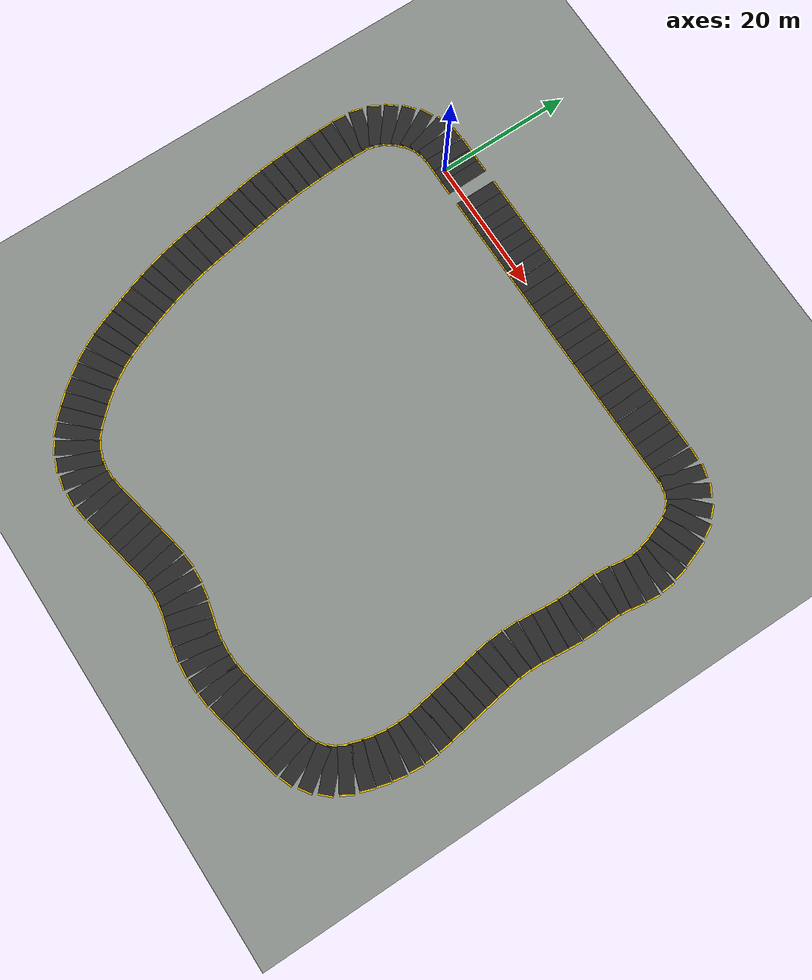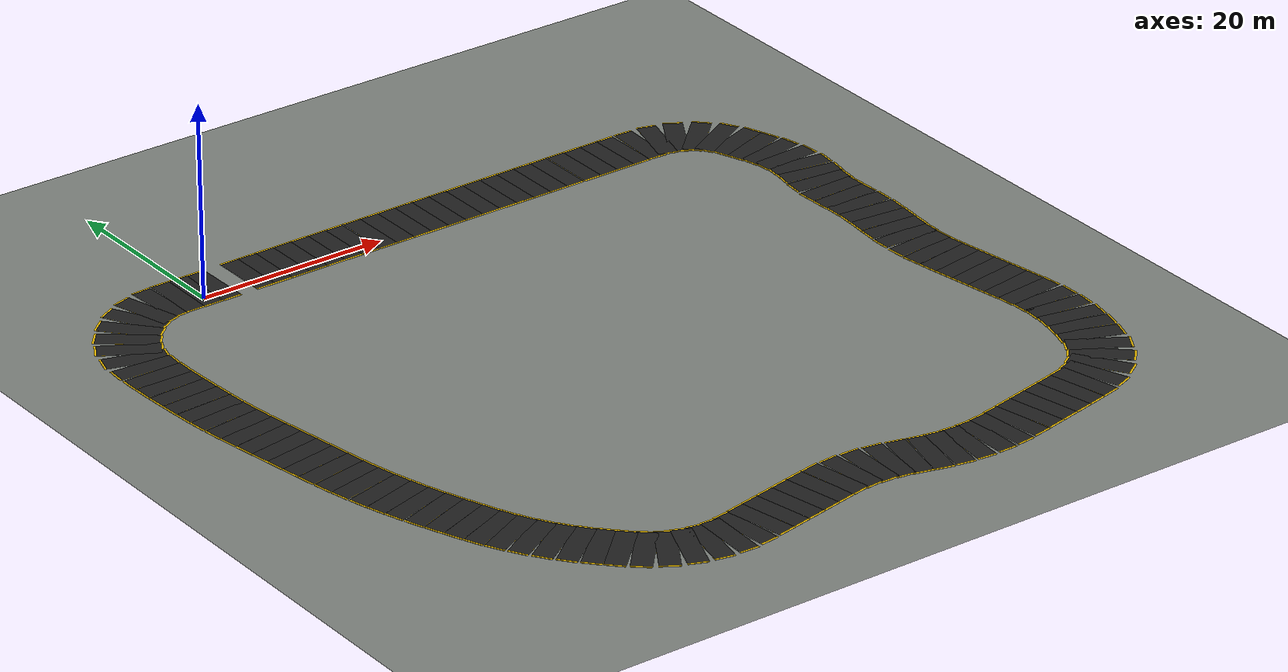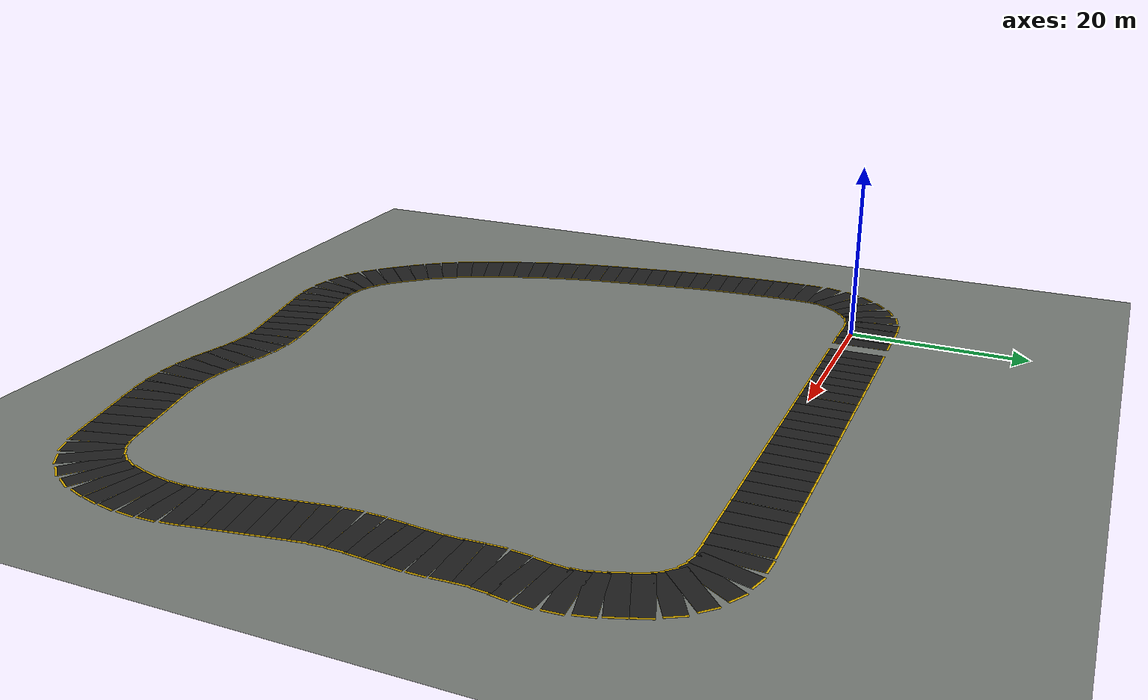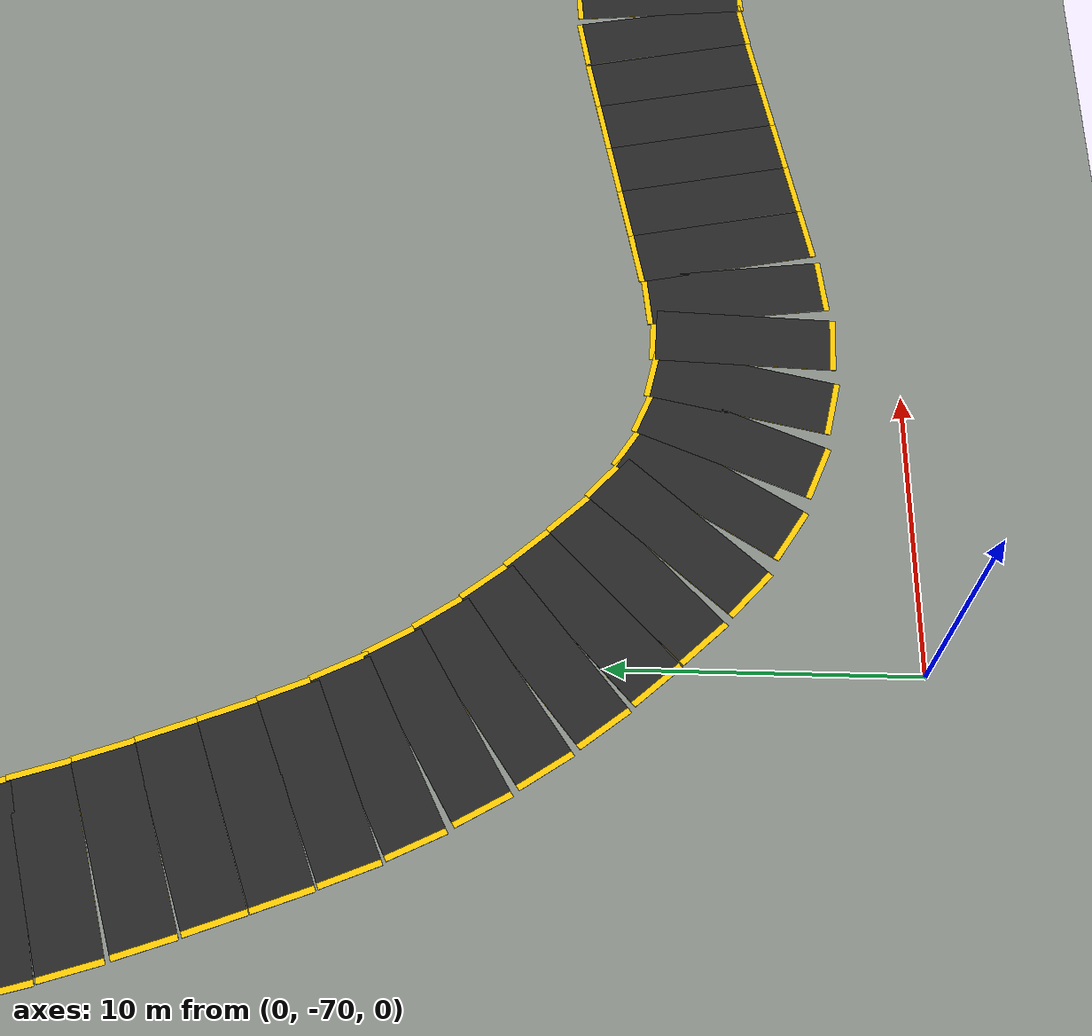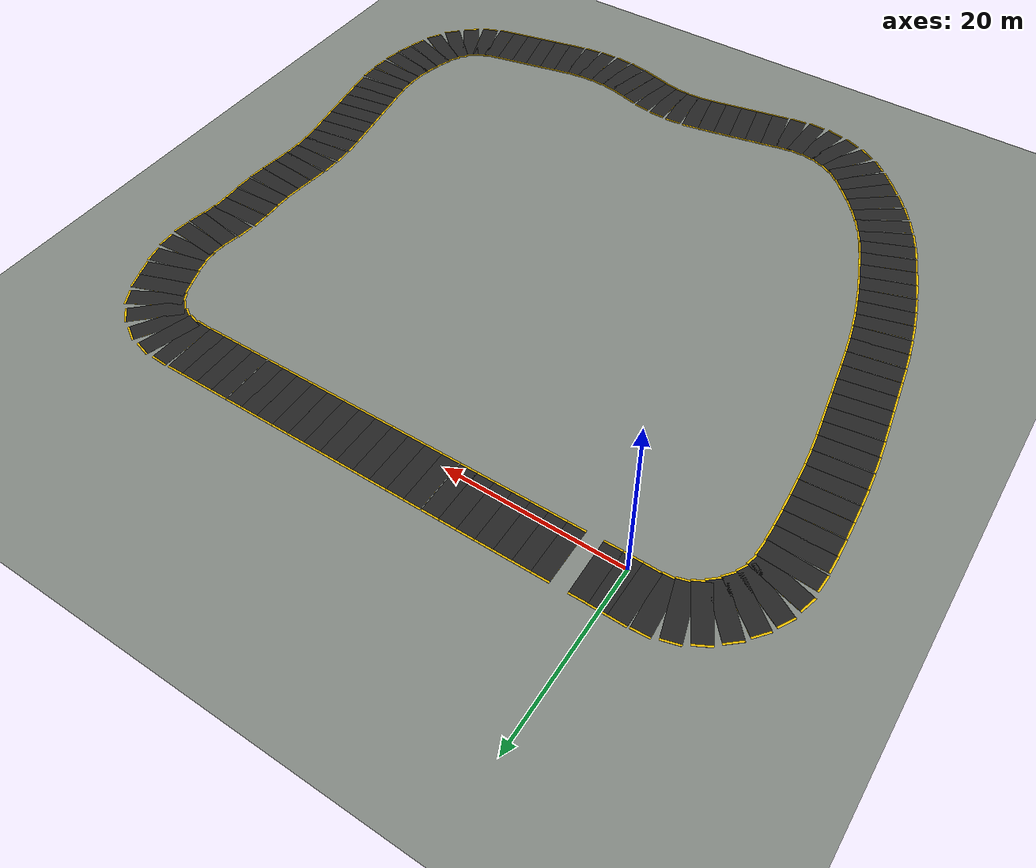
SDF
<sdf version="1.7">
 <world name="custom_road_world">
  <scene><ambient>1.0 1.0 1.0</ambient><background>0.8 0.8 0.8</background></scene>
  <plugin filename="ignition-gazebo-physics-system" name="ignition::gazebo::systems::Physics"/>
  <plugin filename="ignition-gazebo-sensors-system" name="ignition::gazebo::systems::Sensors">
   <render_engine>ogre2</render_engine>
  </plugin>
  <plugin filename="ignition-gazebo-user-commands-system" name="ignition::gazebo::systems::UserCommands"/>
  <plugin filename="ignition-gazebo-scene-broadcaster-system" name="ignition::gazebo::systems::SceneBroadcaster"/>
  <model name="ground_plane">
   <static>true</static>
   <pose>25 -32 -0.005 0 0 0</pose>
   <link name="link">
    <collision name="collision">
     <geometry><plane><normal>0 0 1</normal><size>180 180</size></plane></geometry>
    </collision>
    <visual name="visual">
     <geometry><plane><normal>0 0 1</normal><size>180 180</size></plane></geometry>
     <material>
      <ambient>0.54 0.56 0.54 1</ambient>
      <diffuse>0.54 0.56 0.54 1</diffuse>
      <specular>0.04 0.04 0.04 1</specular>
     </material>
    </visual>
   </link>
  </model>
  <light type="directional" name="sun">
   <pose>0 0 20 0 0 0</pose>
   <diffuse>0.8 0.8 0.8 1</diffuse>
   <specular>0.2 0.2 0.2 1</specular>
   <attenuation>
    <range>1000</range>
    <constant>0.9</constant>
    <linear>0.01</linear>
    <quadratic>0.001</quadratic>
   </attenuation>
   <direction>-0.5 0.3 -0.8</direction>
  </light>
  <model name="elliptical_road">
   <static>true</static>
   <link name="seg_0">
    <pose>6.089 1.763 0.01 0 0 0.006</pose>
    <visual name="yellow_base_0">
     <pose>0 0 0.001 0 0 0</pose>
     <geometry><box><size>2.0 6.4 0.02</size></box></geometry>
     <material>
      <ambient>1.0 0.8 0.0 1.0</ambient>
      <diffuse>1.0 0.8 0.0 1.0</diffuse>
      <specular>0.1 0.1 0.1 1.0</specular>
     </material>
    </visual>
    <visual name="asphalt_top_0">
     <pose>0 0 0.002 0 0 0</pose>
     <geometry><box><size>2.0 6.0 0.02</size></box></geometry>
     <material>
      <ambient>0.15 0.15 0.15 1.0</ambient>
      <diffuse>0.15 0.15 0.15 1.0</diffuse>
      <specular>0.05 0.05 0.05 1.0</specular>
     </material>
    </visual>
    <visual name="center_line_0">
     <pose>0 0 0.003 0 0 0</pose>
     <geometry><box><size>1.0 0.15 0.001</size></box></geometry>
     <material><ambient>0.9 0.9 0.9 1</ambient><diffuse>0.9 0.9 0.9 1</diffuse></material>
    </visual>
    <collision name="collision_0">
     <pose>0 0 0.002 0 0 0</pose>
     <geometry><box><size>2.0 6.0 0.02</size></box></geometry>
    </collision>
   </link>
   <link name="seg_1">
    <pose>8.089 1.776 0.01 0 0 0.006</pose>
    <visual name="yellow_base_1">
     <pose>0 0 0.001 0 0 0</pose>
     <geometry><box><size>2.0 6.4 0.02</size></box></geometry>
     <material>
      <ambient>1.0 0.8 0.0 1.0</ambient>
      <diffuse>1.0 0.8 0.0 1.0</diffuse>
      <specular>0.1 0.1 0.1 1.0</specular>
     </material>
    </visual>
    <visual name="asphalt_top_1">
     <pose>0 0 0.002 0 0 0</pose>
     <geometry><box><size>2.0 6.0 0.02</size></box></geometry>
     <material>
      <ambient>0.15 0.15 0.15 1.0</ambient>
      <diffuse>0.15 0.15 0.15 1.0</diffuse>
      <specular>0.05 0.05 0.05 1.0</specular>
     </material>
    </visual>
    <visual name="center_line_1">
     <pose>0 0 0.003 0 0 0</pose>
     <geometry><box><size>1.0 0.15 0.001</size></box></geometry>
     <material><ambient>0.9 0.9 0.9 1</ambient><diffuse>0.9 0.9 0.9 1</diffuse></material>
    </visual>
    <collision name="collision_1">
     <pose>0 0 0.002 0 0 0</pose>
     <geometry><box><size>2.0 6.0 0.02</size></box></geometry>
    </collision>
   </link>
   <link name="seg_2">
    <pose>10.089 1.789 0.01 0 0 0.006</pose>
    <visual name="yellow_base_2">
     <pose>0 0 0.001 0 0 0</pose>
     <geometry><box><size>2.0 6.4 0.02</size></box></geometry>
     <material>
      <ambient>1.0 0.8 0.0 1.0</ambient>
      <diffuse>1.0 0.8 0.0 1.0</diffuse>
      <specular>0.1 0.1 0.1 1.0</specular>
     </material>
    </visual>
    <visual name="asphalt_top_2">
     <pose>0 0 0.002 0 0 0</pose>
     <geometry><box><size>2.0 6.0 0.02</size></box></geometry>
     <material>
      <ambient>0.15 0.15 0.15 1.0</ambient>
      <diffuse>0.15 0.15 0.15 1.0</diffuse>
      <specular>0.05 0.05 0.05 1.0</specular>
     </material>
    </visual>
    <visual name="center_line_2">
     <pose>0 0 0.003 0 0 0</pose>
     <geometry><box><size>1.0 0.15 0.001</size></box></geometry>
     <material><ambient>0.9 0.9 0.9 1</ambient><diffuse>0.9 0.9 0.9 1</diffuse></material>
    </visual>
    <collision name="collision_2">
     <pose>0 0 0.002 0 0 0</pose>
     <geometry><box><size>2.0 6.0 0.02</size></box></geometry>
    </collision>
   </link>
   <link name="seg_3">
    <pose>12.089 1.802 0.01 0 0 0.006</pose>
    <visual name="yellow_base_3">
     <pose>0 0 0.001 0 0 0</pose>
     <geometry><box><size>2.0 6.4 0.02</size></box></geometry>
     <material>
      <ambient>1.0 0.8 0.0 1.0</ambient>
      <diffuse>1.0 0.8 0.0 1.0</diffuse>
      <specular>0.1 0.1 0.1 1.0</specular>
     </material>
    </visual>
    <visual name="asphalt_top_3">
     <pose>0 0 0.002 0 0 0</pose>
     <geometry><box><size>2.0 6.0 0.02</size></box></geometry>
     <material>
      <ambient>0.15 0.15 0.15 1.0</ambient>
      <diffuse>0.15 0.15 0.15 1.0</diffuse>
      <specular>0.05 0.05 0.05 1.0</specular>
     </material>
    </visual>
    <visual name="center_line_3">
     <pose>0 0 0.003 0 0 0</pose>
     <geometry><box><size>1.0 0.15 0.001</size></box></geometry>
     <material><ambient>0.9 0.9 0.9 1</ambient><diffuse>0.9 0.9 0.9 1</diffuse></material>
    </visual>
    <collision name="collision_3">
     <pose>0 0 0.002 0 0 0</pose>
     <geometry><box><size>2.0 6.0 0.02</size></box></geometry>
    </collision>
   </link>
   <link name="seg_4">
    <pose>14.089 1.815 0.01 0 0 0.006</pose>
    <visual name="yellow_base_4">
     <pose>0 0 0.001 0 0 0</pose>
     <geometry><box><size>2.0 6.4 0.02</size></box></geometry>
     <material>
      <ambient>1.0 0.8 0.0 1.0</ambient>
      <diffuse>1.0 0.8 0.0 1.0</diffuse>
      <specular>0.1 0.1 0.1 1.0</specular>
     </material>
    </visual>
    <visual name="asphalt_top_4">
     <pose>0 0 0.002 0 0 0</pose>
     <geometry><box><size>2.0 6.0 0.02</size></box></geometry>
     <material>
      <ambient>0.15 0.15 0.15 1.0</ambient>
      <diffuse>0.15 0.15 0.15 1.0</diffuse>
      <specular>0.05 0.05 0.05 1.0</specular>
     </material>
    </visual>
    <visual name="center_line_4">
     <pose>0 0 0.003 0 0 0</pose>
     <geometry><box><size>1.0 0.15 0.001</size></box></geometry>
     <material><ambient>0.9 0.9 0.9 1</ambient><diffuse>0.9 0.9 0.9 1</diffuse></material>
    </visual>
    <collision name="collision_4">
     <pose>0 0 0.002 0 0 0</pose>
     <geometry><box><size>2.0 6.0 0.02</size></box></geometry>
    </collision>
   </link>
   <link name="seg_5">
    <pose>16.088 1.827 0.01 0 0 0.006</pose>
    <visual name="yellow_base_5">
     <pose>0 0 0.001 0 0 0</pose>
     <geometry><box><size>2.0 6.4 0.02</size></box></geometry>
     <material>
      <ambient>1.0 0.8 0.0 1.0</ambient>
      <diffuse>1.0 0.8 0.0 1.0</diffuse>
      <specular>0.1 0.1 0.1 1.0</specular>
     </material>
    </visual>
    <visual name="asphalt_top_5">
     <pose>0 0 0.002 0 0 0</pose>
     <geometry><box><size>2.0 6.0 0.02</size></box></geometry>
     <material>
      <ambient>0.15 0.15 0.15 1.0</ambient>
      <diffuse>0.15 0.15 0.15 1.0</diffuse>
      <specular>0.05 0.05 0.05 1.0</specular>
     </material>
    </visual>
    <visual name="center_line_5">
     <pose>0 0 0.003 0 0 0</pose>
     <geometry><box><size>1.0 0.15 0.001</size></box></geometry>
     <material><ambient>0.9 0.9 0.9 1</ambient><diffuse>0.9 0.9 0.9 1</diffuse></material>
    </visual>
    <collision name="collision_5">
     <pose>0 0 0.002 0 0 0</pose>
     <geometry><box><size>2.0 6.0 0.02</size></box></geometry>
    </collision>
   </link>
   <link name="seg_6">
    <pose>17.988 1.840 0.01 0 0 0.006</pose>
    <visual name="yellow_base_6">
     <pose>0 0 0.001 0 0 0</pose>
     <geometry><box><size>2.0 6.4 0.02</size></box></geometry>
     <material>
      <ambient>1.0 0.8 0.0 1.0</ambient>
      <diffuse>1.0 0.8 0.0 1.0</diffuse>
      <specular>0.1 0.1 0.1 1.0</specular>
     </material>
    </visual>
    <visual name="asphalt_top_6">
     <pose>0 0 0.002 0 0 0</pose>
     <geometry><box><size>2.0 6.0 0.02</size></box></geometry>
     <material>
      <ambient>0.15 0.15 0.15 1.0</ambient>
      <diffuse>0.15 0.15 0.15 1.0</diffuse>
      <specular>0.05 0.05 0.05 1.0</specular>
     </material>
    </visual>
    <visual name="center_line_6">
     <pose>0 0 0.003 0 0 0</pose>
     <geometry><box><size>1.0 0.15 0.001</size></box></geometry>
     <material><ambient>0.9 0.9 0.9 1</ambient><diffuse>0.9 0.9 0.9 1</diffuse></material>
    </visual>
    <collision name="collision_6">
     <pose>0 0 0.002 0 0 0</pose>
     <geometry><box><size>2.0 6.0 0.02</size></box></geometry>
    </collision>
   </link>
   <link name="seg_7">
    <pose>20.088 1.853 0.01 0 0 0.006</pose>
    <visual name="yellow_base_7">
     <pose>0 0 0.001 0 0 0</pose>
     <geometry><box><size>2.0 6.4 0.02</size></box></geometry>
     <material>
      <ambient>1.0 0.8 0.0 1.0</ambient>
      <diffuse>1.0 0.8 0.0 1.0</diffuse>
      <specular>0.1 0.1 0.1 1.0</specular>
     </material>
    </visual>
    <visual name="asphalt_top_7">
     <pose>0 0 0.002 0 0 0</pose>
     <geometry><box><size>2.0 6.0 0.02</size></box></geometry>
     <material>
      <ambient>0.15 0.15 0.15 1.0</ambient>
      <diffuse>0.15 0.15 0.15 1.0</diffuse>
      <specular>0.05 0.05 0.05 1.0</specular>
     </material>
    </visual>
    <visual name="center_line_7">
     <pose>0 0 0.003 0 0 0</pose>
     <geometry><box><size>1.0 0.15 0.001</size></box></geometry>
     <material><ambient>0.9 0.9 0.9 1</ambient><diffuse>0.9 0.9 0.9 1</diffuse></material>
    </visual>
    <collision name="collision_7">
     <pose>0 0 0.002 0 0 0</pose>
     <geometry><box><size>2.0 6.0 0.02</size></box></geometry>
    </collision>
   </link>
   <link name="seg_8">
    <pose>22.088 1.866 0.01 0 0 0.006</pose>
    <visual name="yellow_base_8">
     <pose>0 0 0.001 0 0 0</pose>
     <geometry><box><size>2.0 6.4 0.02</size></box></geometry>
     <material>
      <ambient>1.0 0.8 0.0 1.0</ambient>
      <diffuse>1.0 0.8 0.0 1.0</diffuse>
      <specular>0.1 0.1 0.1 1.0</specular>
     </material>
    </visual>
    <visual name="asphalt_top_8">
     <pose>0 0 0.002 0 0 0</pose>
     <geometry><box><size>2.0 6.0 0.02</size></box></geometry>
     <material>
      <ambient>0.15 0.15 0.15 1.0</ambient>
      <diffuse>0.15 0.15 0.15 1.0</diffuse>
      <specular>0.05 0.05 0.05 1.0</specular>
     </material>
    </visual>
    <visual name="center_line_8">
     <pose>0 0 0.003 0 0 0</pose>
     <geometry><box><size>1.0 0.15 0.001</size></box></geometry>
     <material><ambient>0.9 0.9 0.9 1</ambient><diffuse>0.9 0.9 0.9 1</diffuse></material>
    </visual>
    <collision name="collision_8">
     <pose>0 0 0.002 0 0 0</pose>
     <geometry><box><size>2.0 6.0 0.02</size></box></geometry>
    </collision>
   </link>
   <link name="seg_9">
    <pose>24.088 1.879 0.01 0 0 0.006</pose>
    <visual name="yellow_base_9">
     <pose>0 0 0.001 0 0 0</pose>
     <geometry><box><size>2.0 6.4 0.02</size></box></geometry>
     <material>
      <ambient>1.0 0.8 0.0 1.0</ambient>
      <diffuse>1.0 0.8 0.0 1.0</diffuse>
      <specular>0.1 0.1 0.1 1.0</specular>
     </material>
    </visual>
    <visual name="asphalt_top_9">
     <pose>0 0 0.002 0 0 0</pose>
     <geometry><box><size>2.0 6.0 0.02</size></box></geometry>
     <material>
      <ambient>0.15 0.15 0.15 1.0</ambient>
      <diffuse>0.15 0.15 0.15 1.0</diffuse>
      <specular>0.05 0.05 0.05 1.0</specular>
     </material>
    </visual>
    <visual name="center_line_9">
     <pose>0 0 0.003 0 0 0</pose>
     <geometry><box><size>1.0 0.15 0.001</size></box></geometry>
     <material><ambient>0.9 0.9 0.9 1</ambient><diffuse>0.9 0.9 0.9 1</diffuse></material>
    </visual>
    <collision name="collision_9">
     <pose>0 0 0.002 0 0 0</pose>
     <geometry><box><size>2.0 6.0 0.02</size></box></geometry>
    </collision>
   </link>
   <link name="seg_10">
    <pose>26.088 1.891 0.01 0 0 0.006</pose>
    <visual name="yellow_base_10">
     <pose>0 0 0.001 0 0 0</pose>
     <geometry><box><size>2.0 6.4 0.02</size></box></geometry>
     <material>
      <ambient>1.0 0.8 0.0 1.0</ambient>
      <diffuse>1.0 0.8 0.0 1.0</diffuse>
      <specular>0.1 0.1 0.1 1.0</specular>
     </material>
    </visual>
    <visual name="asphalt_top_10">
     <pose>0 0 0.002 0 0 0</pose>
     <geometry><box><size>2.0 6.0 0.02</size></box></geometry>
     <material>
      <ambient>0.15 0.15 0.15 1.0</ambient>
      <diffuse>0.15 0.15 0.15 1.0</diffuse>
      <specular>0.05 0.05 0.05 1.0</specular>
     </material>
    </visual>
    <visual name="center_line_10">
     <pose>0 0 0.003 0 0 0</pose>
     <geometry><box><size>1.0 0.15 0.001</size></box></geometry>
     <material><ambient>0.9 0.9 0.9 1</ambient><diffuse>0.9 0.9 0.9 1</diffuse></material>
    </visual>
    <collision name="collision_10">
     <pose>0 0 0.002 0 0 0</pose>
     <geometry><box><size>2.0 6.0 0.02</size></box></geometry>
    </collision>
   </link>
   <link name="seg_11">
    <pose>28.088 1.904 0.01 0 0 0.006</pose>
    <visual name="yellow_base_11">
     <pose>0 0 0.001 0 0 0</pose>
     <geometry><box><size>2.0 6.4 0.02</size></box></geometry>
     <material>
      <ambient>1.0 0.8 0.0 1.0</ambient>
      <diffuse>1.0 0.8 0.0 1.0</diffuse>
      <specular>0.1 0.1 0.1 1.0</specular>
     </material>
    </visual>
    <visual name="asphalt_top_11">
     <pose>0 0 0.002 0 0 0</pose>
     <geometry><box><size>2.0 6.0 0.02</size></box></geometry>
     <material>
      <ambient>0.15 0.15 0.15 1.0</ambient>
      <diffuse>0.15 0.15 0.15 1.0</diffuse>
      <specular>0.05 0.05 0.05 1.0</specular>
     </material>
    </visual>
    <visual name="center_line_11">
     <pose>0 0 0.003 0 0 0</pose>
     <geometry><box><size>1.0 0.15 0.001</size></box></geometry>
     <material><ambient>0.9 0.9 0.9 1</ambient><diffuse>0.9 0.9 0.9 1</diffuse></material>
    </visual>
    <collision name="collision_11">
     <pose>0 0 0.002 0 0 0</pose>
     <geometry><box><size>2.0 6.0 0.02</size></box></geometry>
    </collision>
   </link>
   <link name="seg_12">
    <pose>30.088 1.917 0.01 0 0 0.006</pose>
    <visual name="yellow_base_12">
     <pose>0 0 0.001 0 0 0</pose>
     <geometry><box><size>2.0 6.4 0.02</size></box></geometry>
     <material>
      <ambient>1.0 0.8 0.0 1.0</ambient>
      <diffuse>1.0 0.8 0.0 1.0</diffuse>
      <specular>0.1 0.1 0.1 1.0</specular>
     </material>
    </visual>
    <visual name="asphalt_top_12">
     <pose>0 0 0.002 0 0 0</pose>
     <geometry><box><size>2.0 6.0 0.02</size></box></geometry>
     <material>
      <ambient>0.15 0.15 0.15 1.0</ambient>
      <diffuse>0.15 0.15 0.15 1.0</diffuse>
      <specular>0.05 0.05 0.05 1.0</specular>
     </material>
    </visual>
    <visual name="center_line_12">
     <pose>0 0 0.003 0 0 0</pose>
     <geometry><box><size>1.0 0.15 0.001</size></box></geometry>
     <material><ambient>0.9 0.9 0.9 1</ambient><diffuse>0.9 0.9 0.9 1</diffuse></material>
    </visual>
    <collision name="collision_12">
     <pose>0 0 0.002 0 0 0</pose>
     <geometry><box><size>2.0 6.0 0.02</size></box></geometry>
    </collision>
   </link>
   <link name="seg_13">
    <pose>32.088 1.930 0.01 0 0 0.006</pose>
    <visual name="yellow_base_13">
     <pose>0 0 0.001 0 0 0</pose>
     <geometry><box><size>2.0 6.4 0.02</size></box></geometry>
     <material>
      <ambient>1.0 0.8 0.0 1.0</ambient>
      <diffuse>1.0 0.8 0.0 1.0</diffuse>
      <specular>0.1 0.1 0.1 1.0</specular>
     </material>
    </visual>
    <visual name="asphalt_top_13">
     <pose>0 0 0.002 0 0 0</pose>
     <geometry><box><size>2.0 6.0 0.02</size></box></geometry>
     <material>
      <ambient>0.15 0.15 0.15 1.0</ambient>
      <diffuse>0.15 0.15 0.15 1.0</diffuse>
      <specular>0.05 0.05 0.05 1.0</specular>
     </material>
    </visual>
    <visual name="center_line_13">
     <pose>0 0 0.003 0 0 0</pose>
     <geometry><box><size>1.0 0.15 0.001</size></box></geometry>
     <material><ambient>0.9 0.9 0.9 1</ambient><diffuse>0.9 0.9 0.9 1</diffuse></material>
    </visual>
    <collision name="collision_13">
     <pose>0 0 0.002 0 0 0</pose>
     <geometry><box><size>2.0 6.0 0.02</size></box></geometry>
    </collision>
   </link>
   <link name="seg_14">
    <pose>34.088 1.943 0.01 0 0 0.006</pose>
    <visual name="yellow_base_14">
     <pose>0 0 0.001 0 0 0</pose>
     <geometry><box><size>2.0 6.4 0.02</size></box></geometry>
     <material>
      <ambient>1.0 0.8 0.0 1.0</ambient>
      <diffuse>1.0 0.8 0.0 1.0</diffuse>
      <specular>0.1 0.1 0.1 1.0</specular>
     </material>
    </visual>
    <visual name="asphalt_top_14">
     <pose>0 0 0.002 0 0 0</pose>
     <geometry><box><size>2.0 6.0 0.02</size></box></geometry>
     <material>
      <ambient>0.15 0.15 0.15 1.0</ambient>
      <diffuse>0.15 0.15 0.15 1.0</diffuse>
      <specular>0.05 0.05 0.05 1.0</specular>
     </material>
    </visual>
    <visual name="center_line_14">
     <pose>0 0 0.003 0 0 0</pose>
     <geometry><box><size>1.0 0.15 0.001</size></box></geometry>
     <material><ambient>0.9 0.9 0.9 1</ambient><diffuse>0.9 0.9 0.9 1</diffuse></material>
    </visual>
    <collision name="collision_14">
     <pose>0 0 0.002 0 0 0</pose>
     <geometry><box><size>2.0 6.0 0.02</size></box></geometry>
    </collision>
   </link>
   <link name="seg_15">
    <pose>36.088 1.956 0.01 0 0 0.006</pose>
    <visual name="yellow_base_15">
     <pose>0 0 0.001 0 0 0</pose>
     <geometry><box><size>2.0 6.4 0.02</size></box></geometry>
     <material>
      <ambient>1.0 0.8 0.0 1.0</ambient>
      <diffuse>1.0 0.8 0.0 1.0</diffuse>
      <specular>0.1 0.1 0.1 1.0</specular>
     </material>
    </visual>
    <visual name="asphalt_top_15">
     <pose>0 0 0.002 0 0 0</pose>
     <geometry><box><size>2.0 6.0 0.02</size></box></geometry>
     <material>
      <ambient>0.15 0.15 0.15 1.0</ambient>
      <diffuse>0.15 0.15 0.15 1.0</diffuse>
      <specular>0.05 0.05 0.05 1.0</specular>
     </material>
    </visual>
    <visual name="center_line_15">
     <pose>0 0 0.003 0 0 0</pose>
     <geometry><box><size>1.0 0.15 0.001</size></box></geometry>
     <material><ambient>0.9 0.9 0.9 1</ambient><diffuse>0.9 0.9 0.9 1</diffuse></material>
    </visual>
    <collision name="collision_15">
     <pose>0 0 0.002 0 0 0</pose>
     <geometry><box><size>2.0 6.0 0.02</size></box></geometry>
    </collision>
   </link>
   <link name="seg_16">
    <pose>38.088 1.968 0.01 0 0 0.006</pose>
    <visual name="yellow_base_16">
     <pose>0 0 0.001 0 0 0</pose>
     <geometry><box><size>2.0 6.4 0.02</size></box></geometry>
     <material>
      <ambient>1.0 0.8 0.0 1.0</ambient>
      <diffuse>1.0 0.8 0.0 1.0</diffuse>
      <specular>0.1 0.1 0.1 1.0</specular>
     </material>
    </visual>
    <visual name="asphalt_top_16">
     <pose>0 0 0.002 0 0 0</pose>
     <geometry><box><size>2.0 6.0 0.02</size></box></geometry>
     <material>
      <ambient>0.15 0.15 0.15 1.0</ambient>
      <diffuse>0.15 0.15 0.15 1.0</diffuse>
      <specular>0.05 0.05 0.05 1.0</specular>
     </material>
    </visual>
    <visual name="center_line_16">
     <pose>0 0 0.003 0 0 0</pose>
     <geometry><box><size>1.0 0.15 0.001</size></box></geometry>
     <material><ambient>0.9 0.9 0.9 1</ambient><diffuse>0.9 0.9 0.9 1</diffuse></material>
    </visual>
    <collision name="collision_16">
     <pose>0 0 0.002 0 0 0</pose>
     <geometry><box><size>2.0 6.0 0.02</size></box></geometry>
    </collision>
   </link>
   <link name="seg_17">
    <pose>40.088 1.981 0.01 0 0 0.006</pose>
    <visual name="yellow_base_17">
     <pose>0 0 0.001 0 0 0</pose>
     <geometry><box><size>2.0 6.4 0.02</size></box></geometry>
     <material>
      <ambient>1.0 0.8 0.0 1.0</ambient>
      <diffuse>1.0 0.8 0.0 1.0</diffuse>
      <specular>0.1 0.1 0.1 1.0</specular>
     </material>
    </visual>
    <visual name="asphalt_top_17">
     <pose>0 0 0.002 0 0 0</pose>
     <geometry><box><size>2.0 6.0 0.02</size></box></geometry>
     <material>
      <ambient>0.15 0.15 0.15 1.0</ambient>
      <diffuse>0.15 0.15 0.15 1.0</diffuse>
      <specular>0.05 0.05 0.05 1.0</specular>
     </material>
    </visual>
    <visual name="center_line_17">
     <pose>0 0 0.003 0 0 0</pose>
     <geometry><box><size>1.0 0.15 0.001</size></box></geometry>
     <material><ambient>0.9 0.9 0.9 1</ambient><diffuse>0.9 0.9 0.9 1</diffuse></material>
    </visual>
    <collision name="collision_17">
     <pose>0 0 0.002 0 0 0</pose>
     <geometry><box><size>2.0 6.0 0.02</size></box></geometry>
    </collision>
   </link>
   <link name="seg_18">
    <pose>41.988 1.993 0.01 0 0 0.006</pose>
    <visual name="yellow_base_18">
     <pose>0 0 0.001 0 0 0</pose>
     <geometry><box><size>2.0 6.4 0.02</size></box></geometry>
     <material>
      <ambient>1.0 0.8 0.0 1.0</ambient>
      <diffuse>1.0 0.8 0.0 1.0</diffuse>
      <specular>0.1 0.1 0.1 1.0</specular>
     </material>
    </visual>
    <visual name="asphalt_top_18">
     <pose>0 0 0.002 0 0 0</pose>
     <geometry><box><size>2.0 6.0 0.02</size></box></geometry>
     <material>
      <ambient>0.15 0.15 0.15 1.0</ambient>
      <diffuse>0.15 0.15 0.15 1.0</diffuse>
      <specular>0.05 0.05 0.05 1.0</specular>
     </material>
    </visual>
    <visual name="center_line_18">
     <pose>0 0 0.003 0 0 0</pose>
     <geometry><box><size>1.0 0.15 0.001</size></box></geometry>
     <material><ambient>0.9 0.9 0.9 1</ambient><diffuse>0.9 0.9 0.9 1</diffuse></material>
    </visual>
    <collision name="collision_18">
     <pose>0 0 0.002 0 0 0</pose>
     <geometry><box><size>2.0 6.0 0.02</size></box></geometry>
    </collision>
   </link>
   <link name="seg_19">
    <pose>44.088 2.007 0.01 0 0 0.006</pose>
    <visual name="yellow_base_19">
     <pose>0 0 0.001 0 0 0</pose>
     <geometry><box><size>2.0 6.4 0.02</size></box></geometry>
     <material>
      <ambient>1.0 0.8 0.0 1.0</ambient>
      <diffuse>1.0 0.8 0.0 1.0</diffuse>
      <specular>0.1 0.1 0.1 1.0</specular>
     </material>
    </visual>
    <visual name="asphalt_top_19">
     <pose>0 0 0.002 0 0 0</pose>
     <geometry><box><size>2.0 6.0 0.02</size></box></geometry>
     <material>
      <ambient>0.15 0.15 0.15 1.0</ambient>
      <diffuse>0.15 0.15 0.15 1.0</diffuse>
      <specular>0.05 0.05 0.05 1.0</specular>
     </material>
    </visual>
    <visual name="center_line_19">
     <pose>0 0 0.003 0 0 0</pose>
     <geometry><box><size>1.0 0.15 0.001</size></box></geometry>
     <material><ambient>0.9 0.9 0.9 1</ambient><diffuse>0.9 0.9 0.9 1</diffuse></material>
    </visual>
    <collision name="collision_19">
     <pose>0 0 0.002 0 0 0</pose>
     <geometry><box><size>2.0 6.0 0.02</size></box></geometry>
    </collision>
   </link>
   <link name="seg_20">
    <pose>46.088 2.020 0.01 0 0 0.006</pose>
    <visual name="yellow_base_20">
     <pose>0 0 0.001 0 0 0</pose>
     <geometry><box><size>2.0 6.4 0.02</size></box></geometry>
     <material>
      <ambient>1.0 0.8 0.0 1.0</ambient>
      <diffuse>1.0 0.8 0.0 1.0</diffuse>
      <specular>0.1 0.1 0.1 1.0</specular>
     </material>
    </visual>
    <visual name="asphalt_top_20">
     <pose>0 0 0.002 0 0 0</pose>
     <geometry><box><size>2.0 6.0 0.02</size></box></geometry>
     <material>
      <ambient>0.15 0.15 0.15 1.0</ambient>
      <diffuse>0.15 0.15 0.15 1.0</diffuse>
      <specular>0.05 0.05 0.05 1.0</specular>
     </material>
    </visual>
    <visual name="center_line_20">
     <pose>0 0 0.003 0 0 0</pose>
     <geometry><box><size>1.0 0.15 0.001</size></box></geometry>
     <material><ambient>0.9 0.9 0.9 1</ambient><diffuse>0.9 0.9 0.9 1</diffuse></material>
    </visual>
    <collision name="collision_20">
     <pose>0 0 0.002 0 0 0</pose>
     <geometry><box><size>2.0 6.0 0.02</size></box></geometry>
    </collision>
   </link>
   <link name="seg_21">
    <pose>48.088 2.032 0.01 0 0 0.006</pose>
    <visual name="yellow_base_21">
     <pose>0 0 0.001 0 0 0</pose>
     <geometry><box><size>2.0 6.4 0.02</size></box></geometry>
     <material>
      <ambient>1.0 0.8 0.0 1.0</ambient>
      <diffuse>1.0 0.8 0.0 1.0</diffuse>
      <specular>0.1 0.1 0.1 1.0</specular>
     </material>
    </visual>
    <visual name="asphalt_top_21">
     <pose>0 0 0.002 0 0 0</pose>
     <geometry><box><size>2.0 6.0 0.02</size></box></geometry>
     <material>
      <ambient>0.15 0.15 0.15 1.0</ambient>
      <diffuse>0.15 0.15 0.15 1.0</diffuse>
      <specular>0.05 0.05 0.05 1.0</specular>
     </material>
    </visual>
    <visual name="center_line_21">
     <pose>0 0 0.003 0 0 0</pose>
     <geometry><box><size>1.0 0.15 0.001</size></box></geometry>
     <material><ambient>0.9 0.9 0.9 1</ambient><diffuse>0.9 0.9 0.9 1</diffuse></material>
    </visual>
    <collision name="collision_21">
     <pose>0 0 0.002 0 0 0</pose>
     <geometry><box><size>2.0 6.0 0.02</size></box></geometry>
    </collision>
   </link>
   <link name="seg_22">
    <pose>49.988 2.045 0.01 0 0 0.006</pose>
    <visual name="yellow_base_22">
     <pose>0 0 0.001 0 0 0</pose>
     <geometry><box><size>2.0 6.4 0.02</size></box></geometry>
     <material>
      <ambient>1.0 0.8 0.0 1.0</ambient>
      <diffuse>1.0 0.8 0.0 1.0</diffuse>
      <specular>0.1 0.1 0.1 1.0</specular>
     </material>
    </visual>
    <visual name="asphalt_top_22">
     <pose>0 0 0.002 0 0 0</pose>
     <geometry><box><size>2.0 6.0 0.02</size></box></geometry>
     <material>
      <ambient>0.15 0.15 0.15 1.0</ambient>
      <diffuse>0.15 0.15 0.15 1.0</diffuse>
      <specular>0.05 0.05 0.05 1.0</specular>
     </material>
    </visual>
    <visual name="center_line_22">
     <pose>0 0 0.003 0 0 0</pose>
     <geometry><box><size>1.0 0.15 0.001</size></box></geometry>
     <material><ambient>0.9 0.9 0.9 1</ambient><diffuse>0.9 0.9 0.9 1</diffuse></material>
    </visual>
    <collision name="collision_22">
     <pose>0 0 0.002 0 0 0</pose>
     <geometry><box><size>2.0 6.0 0.02</size></box></geometry>
    </collision>
   </link>
   <link name="seg_23">
    <pose>52.089 2.058 0.01 0 0 -0.053</pose>
    <visual name="yellow_base_23">
     <pose>0 0 0.001 0 0 0</pose>
     <geometry><box><size>2.0 6.4 0.02</size></box></geometry>
     <material>
      <ambient>1.0 0.8 0.0 1.0</ambient>
      <diffuse>1.0 0.8 0.0 1.0</diffuse>
      <specular>0.1 0.1 0.1 1.0</specular>
     </material>
    </visual>
    <visual name="asphalt_top_23">
     <pose>0 0 0.002 0 0 0</pose>
     <geometry><box><size>2.0 6.0 0.02</size></box></geometry>
     <material>
      <ambient>0.15 0.15 0.15 1.0</ambient>
      <diffuse>0.15 0.15 0.15 1.0</diffuse>
      <specular>0.05 0.05 0.05 1.0</specular>
     </material>
    </visual>
    <visual name="center_line_23">
     <pose>0 0 0.003 0 0 0</pose>
     <geometry><box><size>1.0 0.15 0.001</size></box></geometry>
     <material><ambient>0.9 0.9 0.9 1</ambient><diffuse>0.9 0.9 0.9 1</diffuse></material>
    </visual>
    <collision name="collision_23">
     <pose>0 0 0.002 0 0 0</pose>
     <geometry><box><size>2.0 6.0 0.02</size></box></geometry>
    </collision>
   </link>
   <link name="seg_24">
    <pose>54.062 1.953 0.01 0 0 -0.279</pose>
    <visual name="yellow_base_24">
     <pose>0 0 0.001 0 0 0</pose>
     <geometry><box><size>2.0 6.4 0.02</size></box></geometry>
     <material>
      <ambient>1.0 0.8 0.0 1.0</ambient>
      <diffuse>1.0 0.8 0.0 1.0</diffuse>
      <specular>0.1 0.1 0.1 1.0</specular>
     </material>
    </visual>
    <visual name="asphalt_top_24">
     <pose>0 0 0.002 0 0 0</pose>
     <geometry><box><size>2.0 6.0 0.02</size></box></geometry>
     <material>
      <ambient>0.15 0.15 0.15 1.0</ambient>
      <diffuse>0.15 0.15 0.15 1.0</diffuse>
      <specular>0.05 0.05 0.05 1.0</specular>
     </material>
    </visual>
    <visual name="center_line_24">
     <pose>0 0 0.003 0 0 0</pose>
     <geometry><box><size>1.0 0.15 0.001</size></box></geometry>
     <material><ambient>0.9 0.9 0.9 1</ambient><diffuse>0.9 0.9 0.9 1</diffuse></material>
    </visual>
    <collision name="collision_24">
     <pose>0 0 0.002 0 0 0</pose>
     <geometry><box><size>2.0 6.0 0.02</size></box></geometry>
    </collision>
   </link>
   <link name="seg_25">
    <pose>55.924 1.419 0.01 0 0 -0.540</pose>
    <visual name="yellow_base_25">
     <pose>0 0 0.001 0 0 0</pose>
     <geometry><box><size>2.0 6.4 0.02</size></box></geometry>
     <material>
      <ambient>1.0 0.8 0.0 1.0</ambient>
      <diffuse>1.0 0.8 0.0 1.0</diffuse>
      <specular>0.1 0.1 0.1 1.0</specular>
     </material>
    </visual>
    <visual name="asphalt_top_25">
     <pose>0 0 0.002 0 0 0</pose>
     <geometry><box><size>2.0 6.0 0.02</size></box></geometry>
     <material>
      <ambient>0.15 0.15 0.15 1.0</ambient>
      <diffuse>0.15 0.15 0.15 1.0</diffuse>
      <specular>0.05 0.05 0.05 1.0</specular>
     </material>
    </visual>
    <visual name="center_line_25">
     <pose>0 0 0.003 0 0 0</pose>
     <geometry><box><size>1.0 0.15 0.001</size></box></geometry>
     <material><ambient>0.9 0.9 0.9 1</ambient><diffuse>0.9 0.9 0.9 1</diffuse></material>
    </visual>
    <collision name="collision_25">
     <pose>0 0 0.002 0 0 0</pose>
     <geometry><box><size>2.0 6.0 0.02</size></box></geometry>
    </collision>
   </link>
   <link name="seg_26">
    <pose>57.695 0.356 0.01 0 0 -0.802</pose>
    <visual name="yellow_base_26">
     <pose>0 0 0.001 0 0 0</pose>
     <geometry><box><size>2.0 6.4 0.02</size></box></geometry>
     <material>
      <ambient>1.0 0.8 0.0 1.0</ambient>
      <diffuse>1.0 0.8 0.0 1.0</diffuse>
      <specular>0.1 0.1 0.1 1.0</specular>
     </material>
    </visual>
    <visual name="asphalt_top_26">
     <pose>0 0 0.002 0 0 0</pose>
     <geometry><box><size>2.0 6.0 0.02</size></box></geometry>
     <material>
      <ambient>0.15 0.15 0.15 1.0</ambient>
      <diffuse>0.15 0.15 0.15 1.0</diffuse>
      <specular>0.05 0.05 0.05 1.0</specular>
     </material>
    </visual>
    <visual name="center_line_26">
     <pose>0 0 0.003 0 0 0</pose>
     <geometry><box><size>1.0 0.15 0.001</size></box></geometry>
     <material><ambient>0.9 0.9 0.9 1</ambient><diffuse>0.9 0.9 0.9 1</diffuse></material>
    </visual>
    <collision name="collision_26">
     <pose>0 0 0.002 0 0 0</pose>
     <geometry><box><size>2.0 6.0 0.02</size></box></geometry>
    </collision>
   </link>
   <link name="seg_27">
    <pose>59.042 -1.036 0.01 0 0 -1.058</pose>
    <visual name="yellow_base_27">
     <pose>0 0 0.001 0 0 0</pose>
     <geometry><box><size>2.0 6.4 0.02</size></box></geometry>
     <material>
      <ambient>1.0 0.8 0.0 1.0</ambient>
      <diffuse>1.0 0.8 0.0 1.0</diffuse>
      <specular>0.1 0.1 0.1 1.0</specular>
     </material>
    </visual>
    <visual name="asphalt_top_27">
     <pose>0 0 0.002 0 0 0</pose>
     <geometry><box><size>2.0 6.0 0.02</size></box></geometry>
     <material>
      <ambient>0.15 0.15 0.15 1.0</ambient>
      <diffuse>0.15 0.15 0.15 1.0</diffuse>
      <specular>0.05 0.05 0.05 1.0</specular>
     </material>
    </visual>
    <visual name="center_line_27">
     <pose>0 0 0.003 0 0 0</pose>
     <geometry><box><size>1.0 0.15 0.001</size></box></geometry>
     <material><ambient>0.9 0.9 0.9 1</ambient><diffuse>0.9 0.9 0.9 1</diffuse></material>
    </visual>
    <collision name="collision_27">
     <pose>0 0 0.002 0 0 0</pose>
     <geometry><box><size>2.0 6.0 0.02</size></box></geometry>
    </collision>
   </link>
   <link name="seg_28">
    <pose>60.037 -2.804 0.01 0 0 -1.220</pose>
    <visual name="yellow_base_28">
     <pose>0 0 0.001 0 0 0</pose>
     <geometry><box><size>2.0 6.4 0.02</size></box></geometry>
     <material>
      <ambient>1.0 0.8 0.0 1.0</ambient>
      <diffuse>1.0 0.8 0.0 1.0</diffuse>
      <specular>0.1 0.1 0.1 1.0</specular>
     </material>
    </visual>
    <visual name="asphalt_top_28">
     <pose>0 0 0.002 0 0 0</pose>
     <geometry><box><size>2.0 6.0 0.02</size></box></geometry>
     <material>
      <ambient>0.15 0.15 0.15 1.0</ambient>
      <diffuse>0.15 0.15 0.15 1.0</diffuse>
      <specular>0.05 0.05 0.05 1.0</specular>
     </material>
    </visual>
    <visual name="center_line_28">
     <pose>0 0 0.003 0 0 0</pose>
     <geometry><box><size>1.0 0.15 0.001</size></box></geometry>
     <material><ambient>0.9 0.9 0.9 1</ambient><diffuse>0.9 0.9 0.9 1</diffuse></material>
    </visual>
    <collision name="collision_28">
     <pose>0 0 0.002 0 0 0</pose>
     <geometry><box><size>2.0 6.0 0.02</size></box></geometry>
    </collision>
   </link>
   <link name="seg_29">
    <pose>60.723 -4.677 0.01 0 0 -1.238</pose>
    <visual name="yellow_base_29">
     <pose>0 0 0.001 0 0 0</pose>
     <geometry><box><size>2.0 6.4 0.02</size></box></geometry>
     <material>
      <ambient>1.0 0.8 0.0 1.0</ambient>
      <diffuse>1.0 0.8 0.0 1.0</diffuse>
      <specular>0.1 0.1 0.1 1.0</specular>
     </material>
    </visual>
    <visual name="asphalt_top_29">
     <pose>0 0 0.002 0 0 0</pose>
     <geometry><box><size>2.0 6.0 0.02</size></box></geometry>
     <material>
      <ambient>0.15 0.15 0.15 1.0</ambient>
      <diffuse>0.15 0.15 0.15 1.0</diffuse>
      <specular>0.05 0.05 0.05 1.0</specular>
     </material>
    </visual>
    <visual name="center_line_29">
     <pose>0 0 0.003 0 0 0</pose>
     <geometry><box><size>1.0 0.15 0.001</size></box></geometry>
     <material><ambient>0.9 0.9 0.9 1</ambient><diffuse>0.9 0.9 0.9 1</diffuse></material>
    </visual>
    <collision name="collision_29">
     <pose>0 0 0.002 0 0 0</pose>
     <geometry><box><size>2.0 6.0 0.02</size></box></geometry>
    </collision>
   </link>
   <link name="seg_30">
    <pose>61.367 -6.536 0.01 0 0 -1.350</pose>
    <visual name="yellow_base_30">
     <pose>0 0 0.001 0 0 0</pose>
     <geometry><box><size>2.0 6.4 0.02</size></box></geometry>
     <material>
      <ambient>1.0 0.8 0.0 1.0</ambient>
      <diffuse>1.0 0.8 0.0 1.0</diffuse>
      <specular>0.1 0.1 0.1 1.0</specular>
     </material>
    </visual>
    <visual name="asphalt_top_30">
     <pose>0 0 0.002 0 0 0</pose>
     <geometry><box><size>2.0 6.0 0.02</size></box></geometry>
     <material>
      <ambient>0.15 0.15 0.15 1.0</ambient>
      <diffuse>0.15 0.15 0.15 1.0</diffuse>
      <specular>0.05 0.05 0.05 1.0</specular>
     </material>
    </visual>
    <visual name="center_line_30">
     <pose>0 0 0.003 0 0 0</pose>
     <geometry><box><size>1.0 0.15 0.001</size></box></geometry>
     <material><ambient>0.9 0.9 0.9 1</ambient><diffuse>0.9 0.9 0.9 1</diffuse></material>
    </visual>
    <collision name="collision_30">
     <pose>0 0 0.002 0 0 0</pose>
     <geometry><box><size>2.0 6.0 0.02</size></box></geometry>
    </collision>
   </link>
   <link name="seg_31">
    <pose>61.802 -8.470 0.01 0 0 -1.514</pose>
    <visual name="yellow_base_31">
     <pose>0 0 0.001 0 0 0</pose>
     <geometry><box><size>2.0 6.4 0.02</size></box></geometry>
     <material>
      <ambient>1.0 0.8 0.0 1.0</ambient>
      <diffuse>1.0 0.8 0.0 1.0</diffuse>
      <specular>0.1 0.1 0.1 1.0</specular>
     </material>
    </visual>
    <visual name="asphalt_top_31">
     <pose>0 0 0.002 0 0 0</pose>
     <geometry><box><size>2.0 6.0 0.02</size></box></geometry>
     <material>
      <ambient>0.15 0.15 0.15 1.0</ambient>
      <diffuse>0.15 0.15 0.15 1.0</diffuse>
      <specular>0.05 0.05 0.05 1.0</specular>
     </material>
    </visual>
    <visual name="center_line_31">
     <pose>0 0 0.003 0 0 0</pose>
     <geometry><box><size>1.0 0.15 0.001</size></box></geometry>
     <material><ambient>0.9 0.9 0.9 1</ambient><diffuse>0.9 0.9 0.9 1</diffuse></material>
    </visual>
    <collision name="collision_31">
     <pose>0 0 0.002 0 0 0</pose>
     <geometry><box><size>2.0 6.0 0.02</size></box></geometry>
    </collision>
   </link>
   <link name="seg_32">
    <pose>61.914 -10.453 0.01 0 0 -1.678</pose>
    <visual name="yellow_base_32">
     <pose>0 0 0.001 0 0 0</pose>
     <geometry><box><size>2.0 6.4 0.02</size></box></geometry>
     <material>
      <ambient>1.0 0.8 0.0 1.0</ambient>
      <diffuse>1.0 0.8 0.0 1.0</diffuse>
      <specular>0.1 0.1 0.1 1.0</specular>
     </material>
    </visual>
    <visual name="asphalt_top_32">
     <pose>0 0 0.002 0 0 0</pose>
     <geometry><box><size>2.0 6.0 0.02</size></box></geometry>
     <material>
      <ambient>0.15 0.15 0.15 1.0</ambient>
      <diffuse>0.15 0.15 0.15 1.0</diffuse>
      <specular>0.05 0.05 0.05 1.0</specular>
     </material>
    </visual>
    <visual name="center_line_32">
     <pose>0 0 0.003 0 0 0</pose>
     <geometry><box><size>1.0 0.15 0.001</size></box></geometry>
     <material><ambient>0.9 0.9 0.9 1</ambient><diffuse>0.9 0.9 0.9 1</diffuse></material>
    </visual>
    <collision name="collision_32">
     <pose>0 0 0.002 0 0 0</pose>
     <geometry><box><size>2.0 6.0 0.02</size></box></geometry>
    </collision>
   </link>
   <link name="seg_33">
    <pose>61.696 -12.492 0.01 0 0 -1.740</pose>
    <visual name="yellow_base_33">
     <pose>0 0 0.001 0 0 0</pose>
     <geometry><box><size>2.0 6.4 0.02</size></box></geometry>
     <material>
      <ambient>1.0 0.8 0.0 1.0</ambient>
      <diffuse>1.0 0.8 0.0 1.0</diffuse>
      <specular>0.1 0.1 0.1 1.0</specular>
     </material>
    </visual>
    <visual name="asphalt_top_33">
     <pose>0 0 0.002 0 0 0</pose>
     <geometry><box><size>2.0 6.0 0.02</size></box></geometry>
     <material>
      <ambient>0.15 0.15 0.15 1.0</ambient>
      <diffuse>0.15 0.15 0.15 1.0</diffuse>
      <specular>0.05 0.05 0.05 1.0</specular>
     </material>
    </visual>
    <visual name="center_line_33">
     <pose>0 0 0.003 0 0 0</pose>
     <geometry><box><size>1.0 0.15 0.001</size></box></geometry>
     <material><ambient>0.9 0.9 0.9 1</ambient><diffuse>0.9 0.9 0.9 1</diffuse></material>
    </visual>
    <collision name="collision_33">
     <pose>0 0 0.002 0 0 0</pose>
     <geometry><box><size>2.0 6.0 0.02</size></box></geometry>
    </collision>
   </link>
   <link name="seg_34">
    <pose>61.367 -14.419 0.01 0 0 -1.657</pose>
    <visual name="yellow_base_34">
     <pose>0 0 0.001 0 0 0</pose>
     <geometry><box><size>2.0 6.4 0.02</size></box></geometry>
     <material>
      <ambient>1.0 0.8 0.0 1.0</ambient>
      <diffuse>1.0 0.8 0.0 1.0</diffuse>
      <specular>0.1 0.1 0.1 1.0</specular>
     </material>
    </visual>
    <visual name="asphalt_top_34">
     <pose>0 0 0.002 0 0 0</pose>
     <geometry><box><size>2.0 6.0 0.02</size></box></geometry>
     <material>
      <ambient>0.15 0.15 0.15 1.0</ambient>
      <diffuse>0.15 0.15 0.15 1.0</diffuse>
      <specular>0.05 0.05 0.05 1.0</specular>
     </material>
    </visual>
    <visual name="center_line_34">
     <pose>0 0 0.003 0 0 0</pose>
     <geometry><box><size>1.0 0.15 0.001</size></box></geometry>
     <material><ambient>0.9 0.9 0.9 1</ambient><diffuse>0.9 0.9 0.9 1</diffuse></material>
    </visual>
    <collision name="collision_34">
     <pose>0 0 0.002 0 0 0</pose>
     <geometry><box><size>2.0 6.0 0.02</size></box></geometry>
    </collision>
   </link>
   <link name="seg_35">
    <pose>61.196 -16.406 0.01 0 0 -1.543</pose>
    <visual name="yellow_base_35">
     <pose>0 0 0.001 0 0 0</pose>
     <geometry><box><size>2.0 6.4 0.02</size></box></geometry>
     <material>
      <ambient>1.0 0.8 0.0 1.0</ambient>
      <diffuse>1.0 0.8 0.0 1.0</diffuse>
      <specular>0.1 0.1 0.1 1.0</specular>
     </material>
    </visual>
    <visual name="asphalt_top_35">
     <pose>0 0 0.002 0 0 0</pose>
     <geometry><box><size>2.0 6.0 0.02</size></box></geometry>
     <material>
      <ambient>0.15 0.15 0.15 1.0</ambient>
      <diffuse>0.15 0.15 0.15 1.0</diffuse>
      <specular>0.05 0.05 0.05 1.0</specular>
     </material>
    </visual>
    <visual name="center_line_35">
     <pose>0 0 0.003 0 0 0</pose>
     <geometry><box><size>1.0 0.15 0.001</size></box></geometry>
     <material><ambient>0.9 0.9 0.9 1</ambient><diffuse>0.9 0.9 0.9 1</diffuse></material>
    </visual>
    <collision name="collision_35">
     <pose>0 0 0.002 0 0 0</pose>
     <geometry><box><size>2.0 6.0 0.02</size></box></geometry>
    </collision>
   </link>
   <link name="seg_36">
    <pose>61.253 -18.443 0.01 0 0 -1.524</pose>
    <visual name="yellow_base_36">
     <pose>0 0 0.001 0 0 0</pose>
     <geometry><box><size>2.0 6.4 0.02</size></box></geometry>
     <material>
      <ambient>1.0 0.8 0.0 1.0</ambient>
      <diffuse>1.0 0.8 0.0 1.0</diffuse>
      <specular>0.1 0.1 0.1 1.0</specular>
     </material>
    </visual>
    <visual name="asphalt_top_36">
     <pose>0 0 0.002 0 0 0</pose>
     <geometry><box><size>2.0 6.0 0.02</size></box></geometry>
     <material>
      <ambient>0.15 0.15 0.15 1.0</ambient>
      <diffuse>0.15 0.15 0.15 1.0</diffuse>
      <specular>0.05 0.05 0.05 1.0</specular>
     </material>
    </visual>
    <visual name="center_line_36">
     <pose>0 0 0.003 0 0 0</pose>
     <geometry><box><size>1.0 0.15 0.001</size></box></geometry>
     <material><ambient>0.9 0.9 0.9 1</ambient><diffuse>0.9 0.9 0.9 1</diffuse></material>
    </visual>
    <collision name="collision_36">
     <pose>0 0 0.002 0 0 0</pose>
     <geometry><box><size>2.0 6.0 0.02</size></box></geometry>
    </collision>
   </link>
   <link name="seg_37">
    <pose>61.346 -20.426 0.01 0 0 -1.590</pose>
    <visual name="yellow_base_37">
     <pose>0 0 0.001 0 0 0</pose>
     <geometry><box><size>2.0 6.4 0.02</size></box></geometry>
     <material>
      <ambient>1.0 0.8 0.0 1.0</ambient>
      <diffuse>1.0 0.8 0.0 1.0</diffuse>
      <specular>0.1 0.1 0.1 1.0</specular>
     </material>
    </visual>
    <visual name="asphalt_top_37">
     <pose>0 0 0.002 0 0 0</pose>
     <geometry><box><size>2.0 6.0 0.02</size></box></geometry>
     <material>
      <ambient>0.15 0.15 0.15 1.0</ambient>
      <diffuse>0.15 0.15 0.15 1.0</diffuse>
      <specular>0.05 0.05 0.05 1.0</specular>
     </material>
    </visual>
    <visual name="center_line_37">
     <pose>0 0 0.003 0 0 0</pose>
     <geometry><box><size>1.0 0.15 0.001</size></box></geometry>
     <material><ambient>0.9 0.9 0.9 1</ambient><diffuse>0.9 0.9 0.9 1</diffuse></material>
    </visual>
    <collision name="collision_37">
     <pose>0 0 0.002 0 0 0</pose>
     <geometry><box><size>2.0 6.0 0.02</size></box></geometry>
    </collision>
   </link>
   <link name="seg_38">
    <pose>61.307 -22.448 0.01 0 0 -1.655</pose>
    <visual name="yellow_base_38">
     <pose>0 0 0.001 0 0 0</pose>
     <geometry><box><size>2.0 6.4 0.02</size></box></geometry>
     <material>
      <ambient>1.0 0.8 0.0 1.0</ambient>
      <diffuse>1.0 0.8 0.0 1.0</diffuse>
      <specular>0.1 0.1 0.1 1.0</specular>
     </material>
    </visual>
    <visual name="asphalt_top_38">
     <pose>0 0 0.002 0 0 0</pose>
     <geometry><box><size>2.0 6.0 0.02</size></box></geometry>
     <material>
      <ambient>0.15 0.15 0.15 1.0</ambient>
      <diffuse>0.15 0.15 0.15 1.0</diffuse>
      <specular>0.05 0.05 0.05 1.0</specular>
     </material>
    </visual>
    <visual name="center_line_38">
     <pose>0 0 0.003 0 0 0</pose>
     <geometry><box><size>1.0 0.15 0.001</size></box></geometry>
     <material><ambient>0.9 0.9 0.9 1</ambient><diffuse>0.9 0.9 0.9 1</diffuse></material>
    </visual>
    <collision name="collision_38">
     <pose>0 0 0.002 0 0 0</pose>
     <geometry><box><size>2.0 6.0 0.02</size></box></geometry>
    </collision>
   </link>
   <link name="seg_39">
    <pose>61.141 -24.423 0.01 0 0 -1.672</pose>
    <visual name="yellow_base_39">
     <pose>0 0 0.001 0 0 0</pose>
     <geometry><box><size>2.0 6.4 0.02</size></box></geometry>
     <material>
      <ambient>1.0 0.8 0.0 1.0</ambient>
      <diffuse>1.0 0.8 0.0 1.0</diffuse>
      <specular>0.1 0.1 0.1 1.0</specular>
     </material>
    </visual>
    <visual name="asphalt_top_39">
     <pose>0 0 0.002 0 0 0</pose>
     <geometry><box><size>2.0 6.0 0.02</size></box></geometry>
     <material>
      <ambient>0.15 0.15 0.15 1.0</ambient>
      <diffuse>0.15 0.15 0.15 1.0</diffuse>
      <specular>0.05 0.05 0.05 1.0</specular>
     </material>
    </visual>
    <visual name="center_line_39">
     <pose>0 0 0.003 0 0 0</pose>
     <geometry><box><size>1.0 0.15 0.001</size></box></geometry>
     <material><ambient>0.9 0.9 0.9 1</ambient><diffuse>0.9 0.9 0.9 1</diffuse></material>
    </visual>
    <collision name="collision_39">
     <pose>0 0 0.002 0 0 0</pose>
     <geometry><box><size>2.0 6.0 0.02</size></box></geometry>
    </collision>
   </link>
   <link name="seg_40">
    <pose>60.940 -26.409 0.01 0 0 -1.646</pose>
    <visual name="yellow_base_40">
     <pose>0 0 0.001 0 0 0</pose>
     <geometry><box><size>2.0 6.4 0.02</size></box></geometry>
     <material>
      <ambient>1.0 0.8 0.0 1.0</ambient>
      <diffuse>1.0 0.8 0.0 1.0</diffuse>
      <specular>0.1 0.1 0.1 1.0</specular>
     </material>
    </visual>
    <visual name="asphalt_top_40">
     <pose>0 0 0.002 0 0 0</pose>
     <geometry><box><size>2.0 6.0 0.02</size></box></geometry>
     <material>
      <ambient>0.15 0.15 0.15 1.0</ambient>
      <diffuse>0.15 0.15 0.15 1.0</diffuse>
      <specular>0.05 0.05 0.05 1.0</specular>
     </material>
    </visual>
    <visual name="center_line_40">
     <pose>0 0 0.003 0 0 0</pose>
     <geometry><box><size>1.0 0.15 0.001</size></box></geometry>
     <material><ambient>0.9 0.9 0.9 1</ambient><diffuse>0.9 0.9 0.9 1</diffuse></material>
    </visual>
    <collision name="collision_40">
     <pose>0 0 0.002 0 0 0</pose>
     <geometry><box><size>2.0 6.0 0.02</size></box></geometry>
    </collision>
   </link>
   <link name="seg_41">
    <pose>60.790 -28.401 0.01 0 0 -1.571</pose>
    <visual name="yellow_base_41">
     <pose>0 0 0.001 0 0 0</pose>
     <geometry><box><size>2.0 6.4 0.02</size></box></geometry>
     <material>
      <ambient>1.0 0.8 0.0 1.0</ambient>
      <diffuse>1.0 0.8 0.0 1.0</diffuse>
      <specular>0.1 0.1 0.1 1.0</specular>
     </material>
    </visual>
    <visual name="asphalt_top_41">
     <pose>0 0 0.002 0 0 0</pose>
     <geometry><box><size>2.0 6.0 0.02</size></box></geometry>
     <material>
      <ambient>0.15 0.15 0.15 1.0</ambient>
      <diffuse>0.15 0.15 0.15 1.0</diffuse>
      <specular>0.05 0.05 0.05 1.0</specular>
     </material>
    </visual>
    <visual name="center_line_41">
     <pose>0 0 0.003 0 0 0</pose>
     <geometry><box><size>1.0 0.15 0.001</size></box></geometry>
     <material><ambient>0.9 0.9 0.9 1</ambient><diffuse>0.9 0.9 0.9 1</diffuse></material>
    </visual>
    <collision name="collision_41">
     <pose>0 0 0.002 0 0 0</pose>
     <geometry><box><size>2.0 6.0 0.02</size></box></geometry>
    </collision>
   </link>
   <link name="seg_42">
    <pose>60.789 -30.461 0.01 0 0 -1.493</pose>
    <visual name="yellow_base_42">
     <pose>0 0 0.001 0 0 0</pose>
     <geometry><box><size>2.0 6.4 0.02</size></box></geometry>
     <material>
      <ambient>1.0 0.8 0.0 1.0</ambient>
      <diffuse>1.0 0.8 0.0 1.0</diffuse>
      <specular>0.1 0.1 0.1 1.0</specular>
     </material>
    </visual>
    <visual name="asphalt_top_42">
     <pose>0 0 0.002 0 0 0</pose>
     <geometry><box><size>2.0 6.0 0.02</size></box></geometry>
     <material>
      <ambient>0.15 0.15 0.15 1.0</ambient>
      <diffuse>0.15 0.15 0.15 1.0</diffuse>
      <specular>0.05 0.05 0.05 1.0</specular>
     </material>
    </visual>
    <visual name="center_line_42">
     <pose>0 0 0.003 0 0 0</pose>
     <geometry><box><size>1.0 0.15 0.001</size></box></geometry>
     <material><ambient>0.9 0.9 0.9 1</ambient><diffuse>0.9 0.9 0.9 1</diffuse></material>
    </visual>
    <collision name="collision_42">
     <pose>0 0 0.002 0 0 0</pose>
     <geometry><box><size>2.0 6.0 0.02</size></box></geometry>
    </collision>
   </link>
   <link name="seg_43">
    <pose>60.941 -32.421 0.01 0 0 -1.426</pose>
    <visual name="yellow_base_43">
     <pose>0 0 0.001 0 0 0</pose>
     <geometry><box><size>2.0 6.4 0.02</size></box></geometry>
     <material>
      <ambient>1.0 0.8 0.0 1.0</ambient>
      <diffuse>1.0 0.8 0.0 1.0</diffuse>
      <specular>0.1 0.1 0.1 1.0</specular>
     </material>
    </visual>
    <visual name="asphalt_top_43">
     <pose>0 0 0.002 0 0 0</pose>
     <geometry><box><size>2.0 6.0 0.02</size></box></geometry>
     <material>
      <ambient>0.15 0.15 0.15 1.0</ambient>
      <diffuse>0.15 0.15 0.15 1.0</diffuse>
      <specular>0.05 0.05 0.05 1.0</specular>
     </material>
    </visual>
    <visual name="center_line_43">
     <pose>0 0 0.003 0 0 0</pose>
     <geometry><box><size>1.0 0.15 0.001</size></box></geometry>
     <material><ambient>0.9 0.9 0.9 1</ambient><diffuse>0.9 0.9 0.9 1</diffuse></material>
    </visual>
    <collision name="collision_43">
     <pose>0 0 0.002 0 0 0</pose>
     <geometry><box><size>2.0 6.0 0.02</size></box></geometry>
    </collision>
   </link>
   <link name="seg_44">
    <pose>61.233 -34.421 0.01 0 0 -1.411</pose>
    <visual name="yellow_base_44">
     <pose>0 0 0.001 0 0 0</pose>
     <geometry><box><size>2.0 6.4 0.02</size></box></geometry>
     <material>
      <ambient>1.0 0.8 0.0 1.0</ambient>
      <diffuse>1.0 0.8 0.0 1.0</diffuse>
      <specular>0.1 0.1 0.1 1.0</specular>
     </material>
    </visual>
    <visual name="asphalt_top_44">
     <pose>0 0 0.002 0 0 0</pose>
     <geometry><box><size>2.0 6.0 0.02</size></box></geometry>
     <material>
      <ambient>0.15 0.15 0.15 1.0</ambient>
      <diffuse>0.15 0.15 0.15 1.0</diffuse>
      <specular>0.05 0.05 0.05 1.0</specular>
     </material>
    </visual>
    <visual name="center_line_44">
     <pose>0 0 0.003 0 0 0</pose>
     <geometry><box><size>1.0 0.15 0.001</size></box></geometry>
     <material><ambient>0.9 0.9 0.9 1</ambient><diffuse>0.9 0.9 0.9 1</diffuse></material>
    </visual>
    <collision name="collision_44">
     <pose>0 0 0.002 0 0 0</pose>
     <geometry><box><size>2.0 6.0 0.02</size></box></geometry>
    </collision>
   </link>
   <link name="seg_45">
    <pose>61.553 -36.396 0.01 0 0 -1.411</pose>
    <visual name="yellow_base_45">
     <pose>0 0 0.001 0 0 0</pose>
     <geometry><box><size>2.0 6.4 0.02</size></box></geometry>
     <material>
      <ambient>1.0 0.8 0.0 1.0</ambient>
      <diffuse>1.0 0.8 0.0 1.0</diffuse>
      <specular>0.1 0.1 0.1 1.0</specular>
     </material>
    </visual>
    <visual name="asphalt_top_45">
     <pose>0 0 0.002 0 0 0</pose>
     <geometry><box><size>2.0 6.0 0.02</size></box></geometry>
     <material>
      <ambient>0.15 0.15 0.15 1.0</ambient>
      <diffuse>0.15 0.15 0.15 1.0</diffuse>
      <specular>0.05 0.05 0.05 1.0</specular>
     </material>
    </visual>
    <visual name="center_line_45">
     <pose>0 0 0.003 0 0 0</pose>
     <geometry><box><size>1.0 0.15 0.001</size></box></geometry>
     <material><ambient>0.9 0.9 0.9 1</ambient><diffuse>0.9 0.9 0.9 1</diffuse></material>
    </visual>
    <collision name="collision_45">
     <pose>0 0 0.002 0 0 0</pose>
     <geometry><box><size>2.0 6.0 0.02</size></box></geometry>
    </collision>
   </link>
   <link name="seg_46">
    <pose>61.872 -38.370 0.01 0 0 -1.411</pose>
    <visual name="yellow_base_46">
     <pose>0 0 0.001 0 0 0</pose>
     <geometry><box><size>2.0 6.4 0.02</size></box></geometry>
     <material>
      <ambient>1.0 0.8 0.0 1.0</ambient>
      <diffuse>1.0 0.8 0.0 1.0</diffuse>
      <specular>0.1 0.1 0.1 1.0</specular>
     </material>
    </visual>
    <visual name="asphalt_top_46">
     <pose>0 0 0.002 0 0 0</pose>
     <geometry><box><size>2.0 6.0 0.02</size></box></geometry>
     <material>
      <ambient>0.15 0.15 0.15 1.0</ambient>
      <diffuse>0.15 0.15 0.15 1.0</diffuse>
      <specular>0.05 0.05 0.05 1.0</specular>
     </material>
    </visual>
    <visual name="center_line_46">
     <pose>0 0 0.003 0 0 0</pose>
     <geometry><box><size>1.0 0.15 0.001</size></box></geometry>
     <material><ambient>0.9 0.9 0.9 1</ambient><diffuse>0.9 0.9 0.9 1</diffuse></material>
    </visual>
    <collision name="collision_46">
     <pose>0 0 0.002 0 0 0</pose>
     <geometry><box><size>2.0 6.0 0.02</size></box></geometry>
    </collision>
   </link>
   <link name="seg_47">
    <pose>62.191 -40.344 0.01 0 0 -1.411</pose>
    <visual name="yellow_base_47">
     <pose>0 0 0.001 0 0 0</pose>
     <geometry><box><size>2.0 6.4 0.02</size></box></geometry>
     <material>
      <ambient>1.0 0.8 0.0 1.0</ambient>
      <diffuse>1.0 0.8 0.0 1.0</diffuse>
      <specular>0.1 0.1 0.1 1.0</specular>
     </material>
    </visual>
    <visual name="asphalt_top_47">
     <pose>0 0 0.002 0 0 0</pose>
     <geometry><box><size>2.0 6.0 0.02</size></box></geometry>
     <material>
      <ambient>0.15 0.15 0.15 1.0</ambient>
      <diffuse>0.15 0.15 0.15 1.0</diffuse>
      <specular>0.05 0.05 0.05 1.0</specular>
     </material>
    </visual>
    <visual name="center_line_47">
     <pose>0 0 0.003 0 0 0</pose>
     <geometry><box><size>1.0 0.15 0.001</size></box></geometry>
     <material><ambient>0.9 0.9 0.9 1</ambient><diffuse>0.9 0.9 0.9 1</diffuse></material>
    </visual>
    <collision name="collision_47">
     <pose>0 0 0.002 0 0 0</pose>
     <geometry><box><size>2.0 6.0 0.02</size></box></geometry>
    </collision>
   </link>
   <link name="seg_48">
    <pose>62.510 -42.319 0.01 0 0 -1.413</pose>
    <visual name="yellow_base_48">
     <pose>0 0 0.001 0 0 0</pose>
     <geometry><box><size>2.0 6.4 0.02</size></box></geometry>
     <material>
      <ambient>1.0 0.8 0.0 1.0</ambient>
      <diffuse>1.0 0.8 0.0 1.0</diffuse>
      <specular>0.1 0.1 0.1 1.0</specular>
     </material>
    </visual>
    <visual name="asphalt_top_48">
     <pose>0 0 0.002 0 0 0</pose>
     <geometry><box><size>2.0 6.0 0.02</size></box></geometry>
     <material>
      <ambient>0.15 0.15 0.15 1.0</ambient>
      <diffuse>0.15 0.15 0.15 1.0</diffuse>
      <specular>0.05 0.05 0.05 1.0</specular>
     </material>
    </visual>
    <visual name="center_line_48">
     <pose>0 0 0.003 0 0 0</pose>
     <geometry><box><size>1.0 0.15 0.001</size></box></geometry>
     <material><ambient>0.9 0.9 0.9 1</ambient><diffuse>0.9 0.9 0.9 1</diffuse></material>
    </visual>
    <collision name="collision_48">
     <pose>0 0 0.002 0 0 0</pose>
     <geometry><box><size>2.0 6.0 0.02</size></box></geometry>
    </collision>
   </link>
   <link name="seg_49">
    <pose>62.812 -44.216 0.01 0 0 -1.463</pose>
    <visual name="yellow_base_49">
     <pose>0 0 0.001 0 0 0</pose>
     <geometry><box><size>2.0 6.4 0.02</size></box></geometry>
     <material>
      <ambient>1.0 0.8 0.0 1.0</ambient>
      <diffuse>1.0 0.8 0.0 1.0</diffuse>
      <specular>0.1 0.1 0.1 1.0</specular>
     </material>
    </visual>
    <visual name="asphalt_top_49">
     <pose>0 0 0.002 0 0 0</pose>
     <geometry><box><size>2.0 6.0 0.02</size></box></geometry>
     <material>
      <ambient>0.15 0.15 0.15 1.0</ambient>
      <diffuse>0.15 0.15 0.15 1.0</diffuse>
      <specular>0.05 0.05 0.05 1.0</specular>
     </material>
    </visual>
    <visual name="center_line_49">
     <pose>0 0 0.003 0 0 0</pose>
     <geometry><box><size>1.0 0.15 0.001</size></box></geometry>
     <material><ambient>0.9 0.9 0.9 1</ambient><diffuse>0.9 0.9 0.9 1</diffuse></material>
    </visual>
    <collision name="collision_49">
     <pose>0 0 0.002 0 0 0</pose>
     <geometry><box><size>2.0 6.0 0.02</size></box></geometry>
    </collision>
   </link>
   <link name="seg_50">
    <pose>63.034 -46.258 0.01 0 0 -1.560</pose>
    <visual name="yellow_base_50">
     <pose>0 0 0.001 0 0 0</pose>
     <geometry><box><size>2.0 6.4 0.02</size></box></geometry>
     <material>
      <ambient>1.0 0.8 0.0 1.0</ambient>
      <diffuse>1.0 0.8 0.0 1.0</diffuse>
      <specular>0.1 0.1 0.1 1.0</specular>
     </material>
    </visual>
    <visual name="asphalt_top_50">
     <pose>0 0 0.002 0 0 0</pose>
     <geometry><box><size>2.0 6.0 0.02</size></box></geometry>
     <material>
      <ambient>0.15 0.15 0.15 1.0</ambient>
      <diffuse>0.15 0.15 0.15 1.0</diffuse>
      <specular>0.05 0.05 0.05 1.0</specular>
     </material>
    </visual>
    <visual name="center_line_50">
     <pose>0 0 0.003 0 0 0</pose>
     <geometry><box><size>1.0 0.15 0.001</size></box></geometry>
     <material><ambient>0.9 0.9 0.9 1</ambient><diffuse>0.9 0.9 0.9 1</diffuse></material>
    </visual>
    <collision name="collision_50">
     <pose>0 0 0.002 0 0 0</pose>
     <geometry><box><size>2.0 6.0 0.02</size></box></geometry>
    </collision>
   </link>
   <link name="seg_51">
    <pose>63.056 -48.228 0.01 0 0 -1.660</pose>
    <visual name="yellow_base_51">
     <pose>0 0 0.001 0 0 0</pose>
     <geometry><box><size>2.0 6.4 0.02</size></box></geometry>
     <material>
      <ambient>1.0 0.8 0.0 1.0</ambient>
      <diffuse>1.0 0.8 0.0 1.0</diffuse>
      <specular>0.1 0.1 0.1 1.0</specular>
     </material>
    </visual>
    <visual name="asphalt_top_51">
     <pose>0 0 0.002 0 0 0</pose>
     <geometry><box><size>2.0 6.0 0.02</size></box></geometry>
     <material>
      <ambient>0.15 0.15 0.15 1.0</ambient>
      <diffuse>0.15 0.15 0.15 1.0</diffuse>
      <specular>0.05 0.05 0.05 1.0</specular>
     </material>
    </visual>
    <visual name="center_line_51">
     <pose>0 0 0.003 0 0 0</pose>
     <geometry><box><size>1.0 0.15 0.001</size></box></geometry>
     <material><ambient>0.9 0.9 0.9 1</ambient><diffuse>0.9 0.9 0.9 1</diffuse></material>
    </visual>
    <collision name="collision_51">
     <pose>0 0 0.002 0 0 0</pose>
     <geometry><box><size>2.0 6.0 0.02</size></box></geometry>
    </collision>
   </link>
   <link name="seg_52">
    <pose>62.870 -50.298 0.01 0 0 -1.760</pose>
    <visual name="yellow_base_52">
     <pose>0 0 0.001 0 0 0</pose>
     <geometry><box><size>2.0 6.4 0.02</size></box></geometry>
     <material>
      <ambient>1.0 0.8 0.0 1.0</ambient>
      <diffuse>1.0 0.8 0.0 1.0</diffuse>
      <specular>0.1 0.1 0.1 1.0</specular>
     </material>
    </visual>
    <visual name="asphalt_top_52">
     <pose>0 0 0.002 0 0 0</pose>
     <geometry><box><size>2.0 6.0 0.02</size></box></geometry>
     <material>
      <ambient>0.15 0.15 0.15 1.0</ambient>
      <diffuse>0.15 0.15 0.15 1.0</diffuse>
      <specular>0.05 0.05 0.05 1.0</specular>
     </material>
    </visual>
    <visual name="center_line_52">
     <pose>0 0 0.003 0 0 0</pose>
     <geometry><box><size>1.0 0.15 0.001</size></box></geometry>
     <material><ambient>0.9 0.9 0.9 1</ambient><diffuse>0.9 0.9 0.9 1</diffuse></material>
    </visual>
    <collision name="collision_52">
     <pose>0 0 0.002 0 0 0</pose>
     <geometry><box><size>2.0 6.0 0.02</size></box></geometry>
    </collision>
   </link>
   <link name="seg_53">
    <pose>62.500 -52.233 0.01 0 0 -1.841</pose>
    <visual name="yellow_base_53">
     <pose>0 0 0.001 0 0 0</pose>
     <geometry><box><size>2.0 6.4 0.02</size></box></geometry>
     <material>
      <ambient>1.0 0.8 0.0 1.0</ambient>
      <diffuse>1.0 0.8 0.0 1.0</diffuse>
      <specular>0.1 0.1 0.1 1.0</specular>
     </material>
    </visual>
    <visual name="asphalt_top_53">
     <pose>0 0 0.002 0 0 0</pose>
     <geometry><box><size>2.0 6.0 0.02</size></box></geometry>
     <material>
      <ambient>0.15 0.15 0.15 1.0</ambient>
      <diffuse>0.15 0.15 0.15 1.0</diffuse>
      <specular>0.05 0.05 0.05 1.0</specular>
     </material>
    </visual>
    <visual name="center_line_53">
     <pose>0 0 0.003 0 0 0</pose>
     <geometry><box><size>1.0 0.15 0.001</size></box></geometry>
     <material><ambient>0.9 0.9 0.9 1</ambient><diffuse>0.9 0.9 0.9 1</diffuse></material>
    </visual>
    <collision name="collision_53">
     <pose>0 0 0.002 0 0 0</pose>
     <geometry><box><size>2.0 6.0 0.02</size></box></geometry>
    </collision>
   </link>
   <link name="seg_54">
    <pose>61.971 -54.144 0.01 0 0 -1.905</pose>
    <visual name="yellow_base_54">
     <pose>0 0 0.001 0 0 0</pose>
     <geometry><box><size>2.0 6.4 0.02</size></box></geometry>
     <material>
      <ambient>1.0 0.8 0.0 1.0</ambient>
      <diffuse>1.0 0.8 0.0 1.0</diffuse>
      <specular>0.1 0.1 0.1 1.0</specular>
     </material>
    </visual>
    <visual name="asphalt_top_54">
     <pose>0 0 0.002 0 0 0</pose>
     <geometry><box><size>2.0 6.0 0.02</size></box></geometry>
     <material>
      <ambient>0.15 0.15 0.15 1.0</ambient>
      <diffuse>0.15 0.15 0.15 1.0</diffuse>
      <specular>0.05 0.05 0.05 1.0</specular>
     </material>
    </visual>
    <visual name="center_line_54">
     <pose>0 0 0.003 0 0 0</pose>
     <geometry><box><size>1.0 0.15 0.001</size></box></geometry>
     <material><ambient>0.9 0.9 0.9 1</ambient><diffuse>0.9 0.9 0.9 1</diffuse></material>
    </visual>
    <collision name="collision_54">
     <pose>0 0 0.002 0 0 0</pose>
     <geometry><box><size>2.0 6.0 0.02</size></box></geometry>
    </collision>
   </link>
   <link name="seg_55">
    <pose>61.303 -56.066 0.01 0 0 -2.103</pose>
    <visual name="yellow_base_55">
     <pose>0 0 0.001 0 0 0</pose>
     <geometry><box><size>2.0 6.4 0.02</size></box></geometry>
     <material>
      <ambient>1.0 0.8 0.0 1.0</ambient>
      <diffuse>1.0 0.8 0.0 1.0</diffuse>
      <specular>0.1 0.1 0.1 1.0</specular>
     </material>
    </visual>
    <visual name="asphalt_top_55">
     <pose>0 0 0.002 0 0 0</pose>
     <geometry><box><size>2.0 6.0 0.02</size></box></geometry>
     <material>
      <ambient>0.15 0.15 0.15 1.0</ambient>
      <diffuse>0.15 0.15 0.15 1.0</diffuse>
      <specular>0.05 0.05 0.05 1.0</specular>
     </material>
    </visual>
    <visual name="center_line_55">
     <pose>0 0 0.003 0 0 0</pose>
     <geometry><box><size>1.0 0.15 0.001</size></box></geometry>
     <material><ambient>0.9 0.9 0.9 1</ambient><diffuse>0.9 0.9 0.9 1</diffuse></material>
    </visual>
    <collision name="collision_55">
     <pose>0 0 0.002 0 0 0</pose>
     <geometry><box><size>2.0 6.0 0.02</size></box></geometry>
    </collision>
   </link>
   <link name="seg_56">
    <pose>60.295 -57.778 0.01 0 0 -2.326</pose>
    <visual name="yellow_base_56">
     <pose>0 0 0.001 0 0 0</pose>
     <geometry><box><size>2.0 6.4 0.02</size></box></geometry>
     <material>
      <ambient>1.0 0.8 0.0 1.0</ambient>
      <diffuse>1.0 0.8 0.0 1.0</diffuse>
      <specular>0.1 0.1 0.1 1.0</specular>
     </material>
    </visual>
    <visual name="asphalt_top_56">
     <pose>0 0 0.002 0 0 0</pose>
     <geometry><box><size>2.0 6.0 0.02</size></box></geometry>
     <material>
      <ambient>0.15 0.15 0.15 1.0</ambient>
      <diffuse>0.15 0.15 0.15 1.0</diffuse>
      <specular>0.05 0.05 0.05 1.0</specular>
     </material>
    </visual>
    <visual name="center_line_56">
     <pose>0 0 0.003 0 0 0</pose>
     <geometry><box><size>1.0 0.15 0.001</size></box></geometry>
     <material><ambient>0.9 0.9 0.9 1</ambient><diffuse>0.9 0.9 0.9 1</diffuse></material>
    </visual>
    <collision name="collision_56">
     <pose>0 0 0.002 0 0 0</pose>
     <geometry><box><size>2.0 6.0 0.02</size></box></geometry>
    </collision>
   </link>
   <link name="seg_57">
    <pose>58.934 -59.224 0.01 0 0 -2.549</pose>
    <visual name="yellow_base_57">
     <pose>0 0 0.001 0 0 0</pose>
     <geometry><box><size>2.0 6.4 0.02</size></box></geometry>
     <material>
      <ambient>1.0 0.8 0.0 1.0</ambient>
      <diffuse>1.0 0.8 0.0 1.0</diffuse>
      <specular>0.1 0.1 0.1 1.0</specular>
     </material>
    </visual>
    <visual name="asphalt_top_57">
     <pose>0 0 0.002 0 0 0</pose>
     <geometry><box><size>2.0 6.0 0.02</size></box></geometry>
     <material>
      <ambient>0.15 0.15 0.15 1.0</ambient>
      <diffuse>0.15 0.15 0.15 1.0</diffuse>
      <specular>0.05 0.05 0.05 1.0</specular>
     </material>
    </visual>
    <visual name="center_line_57">
     <pose>0 0 0.003 0 0 0</pose>
     <geometry><box><size>1.0 0.15 0.001</size></box></geometry>
     <material><ambient>0.9 0.9 0.9 1</ambient><diffuse>0.9 0.9 0.9 1</diffuse></material>
    </visual>
    <collision name="collision_57">
     <pose>0 0 0.002 0 0 0</pose>
     <geometry><box><size>2.0 6.0 0.02</size></box></geometry>
    </collision>
   </link>
   <link name="seg_58">
    <pose>57.286 -60.333 0.01 0 0 -2.769</pose>
    <visual name="yellow_base_58">
     <pose>0 0 0.001 0 0 0</pose>
     <geometry><box><size>2.0 6.4 0.02</size></box></geometry>
     <material>
      <ambient>1.0 0.8 0.0 1.0</ambient>
      <diffuse>1.0 0.8 0.0 1.0</diffuse>
      <specular>0.1 0.1 0.1 1.0</specular>
     </material>
    </visual>
    <visual name="asphalt_top_58">
     <pose>0 0 0.002 0 0 0</pose>
     <geometry><box><size>2.0 6.0 0.02</size></box></geometry>
     <material>
      <ambient>0.15 0.15 0.15 1.0</ambient>
      <diffuse>0.15 0.15 0.15 1.0</diffuse>
      <specular>0.05 0.05 0.05 1.0</specular>
     </material>
    </visual>
    <visual name="center_line_58">
     <pose>0 0 0.003 0 0 0</pose>
     <geometry><box><size>1.0 0.15 0.001</size></box></geometry>
     <material><ambient>0.9 0.9 0.9 1</ambient><diffuse>0.9 0.9 0.9 1</diffuse></material>
    </visual>
    <collision name="collision_58">
     <pose>0 0 0.002 0 0 0</pose>
     <geometry><box><size>2.0 6.0 0.02</size></box></geometry>
    </collision>
   </link>
   <link name="seg_59">
    <pose>55.459 -61.047 0.01 0 0 -2.912</pose>
    <visual name="yellow_base_59">
     <pose>0 0 0.001 0 0 0</pose>
     <geometry><box><size>2.0 6.4 0.02</size></box></geometry>
     <material>
      <ambient>1.0 0.8 0.0 1.0</ambient>
      <diffuse>1.0 0.8 0.0 1.0</diffuse>
      <specular>0.1 0.1 0.1 1.0</specular>
     </material>
    </visual>
    <visual name="asphalt_top_59">
     <pose>0 0 0.002 0 0 0</pose>
     <geometry><box><size>2.0 6.0 0.02</size></box></geometry>
     <material>
      <ambient>0.15 0.15 0.15 1.0</ambient>
      <diffuse>0.15 0.15 0.15 1.0</diffuse>
      <specular>0.05 0.05 0.05 1.0</specular>
     </material>
    </visual>
    <visual name="center_line_59">
     <pose>0 0 0.003 0 0 0</pose>
     <geometry><box><size>1.0 0.15 0.001</size></box></geometry>
     <material><ambient>0.9 0.9 0.9 1</ambient><diffuse>0.9 0.9 0.9 1</diffuse></material>
    </visual>
    <collision name="collision_59">
     <pose>0 0 0.002 0 0 0</pose>
     <geometry><box><size>2.0 6.0 0.02</size></box></geometry>
    </collision>
   </link>
   <link name="seg_60">
    <pose>53.515 -61.501 0.01 0 0 -2.925</pose>
    <visual name="yellow_base_60">
     <pose>0 0 0.001 0 0 0</pose>
     <geometry><box><size>2.0 6.4 0.02</size></box></geometry>
     <material>
      <ambient>1.0 0.8 0.0 1.0</ambient>
      <diffuse>1.0 0.8 0.0 1.0</diffuse>
      <specular>0.1 0.1 0.1 1.0</specular>
     </material>
    </visual>
    <visual name="asphalt_top_60">
     <pose>0 0 0.002 0 0 0</pose>
     <geometry><box><size>2.0 6.0 0.02</size></box></geometry>
     <material>
      <ambient>0.15 0.15 0.15 1.0</ambient>
      <diffuse>0.15 0.15 0.15 1.0</diffuse>
      <specular>0.05 0.05 0.05 1.0</specular>
     </material>
    </visual>
    <visual name="center_line_60">
     <pose>0 0 0.003 0 0 0</pose>
     <geometry><box><size>1.0 0.15 0.001</size></box></geometry>
     <material><ambient>0.9 0.9 0.9 1</ambient><diffuse>0.9 0.9 0.9 1</diffuse></material>
    </visual>
    <collision name="collision_60">
     <pose>0 0 0.002 0 0 0</pose>
     <geometry><box><size>2.0 6.0 0.02</size></box></geometry>
    </collision>
   </link>
   <link name="seg_61">
    <pose>51.562 -61.931 0.01 0 0 -2.925</pose>
    <visual name="yellow_base_61">
     <pose>0 0 0.001 0 0 0</pose>
     <geometry><box><size>2.0 6.4 0.02</size></box></geometry>
     <material>
      <ambient>1.0 0.8 0.0 1.0</ambient>
      <diffuse>1.0 0.8 0.0 1.0</diffuse>
      <specular>0.1 0.1 0.1 1.0</specular>
     </material>
    </visual>
    <visual name="asphalt_top_61">
     <pose>0 0 0.002 0 0 0</pose>
     <geometry><box><size>2.0 6.0 0.02</size></box></geometry>
     <material>
      <ambient>0.15 0.15 0.15 1.0</ambient>
      <diffuse>0.15 0.15 0.15 1.0</diffuse>
      <specular>0.05 0.05 0.05 1.0</specular>
     </material>
    </visual>
    <visual name="center_line_61">
     <pose>0 0 0.003 0 0 0</pose>
     <geometry><box><size>1.0 0.15 0.001</size></box></geometry>
     <material><ambient>0.9 0.9 0.9 1</ambient><diffuse>0.9 0.9 0.9 1</diffuse></material>
    </visual>
    <collision name="collision_61">
     <pose>0 0 0.002 0 0 0</pose>
     <geometry><box><size>2.0 6.0 0.02</size></box></geometry>
    </collision>
   </link>
   <link name="seg_62">
    <pose>49.609 -62.362 0.01 0 0 -2.925</pose>
    <visual name="yellow_base_62">
     <pose>0 0 0.001 0 0 0</pose>
     <geometry><box><size>2.0 6.4 0.02</size></box></geometry>
     <material>
      <ambient>1.0 0.8 0.0 1.0</ambient>
      <diffuse>1.0 0.8 0.0 1.0</diffuse>
      <specular>0.1 0.1 0.1 1.0</specular>
     </material>
    </visual>
    <visual name="asphalt_top_62">
     <pose>0 0 0.002 0 0 0</pose>
     <geometry><box><size>2.0 6.0 0.02</size></box></geometry>
     <material>
      <ambient>0.15 0.15 0.15 1.0</ambient>
      <diffuse>0.15 0.15 0.15 1.0</diffuse>
      <specular>0.05 0.05 0.05 1.0</specular>
     </material>
    </visual>
    <visual name="center_line_62">
     <pose>0 0 0.003 0 0 0</pose>
     <geometry><box><size>1.0 0.15 0.001</size></box></geometry>
     <material><ambient>0.9 0.9 0.9 1</ambient><diffuse>0.9 0.9 0.9 1</diffuse></material>
    </visual>
    <collision name="collision_62">
     <pose>0 0 0.002 0 0 0</pose>
     <geometry><box><size>2.0 6.0 0.02</size></box></geometry>
    </collision>
   </link>
   <link name="seg_63">
    <pose>47.656 -62.793 0.01 0 0 -2.925</pose>
    <visual name="yellow_base_63">
     <pose>0 0 0.001 0 0 0</pose>
     <geometry><box><size>2.0 6.4 0.02</size></box></geometry>
     <material>
      <ambient>1.0 0.8 0.0 1.0</ambient>
      <diffuse>1.0 0.8 0.0 1.0</diffuse>
      <specular>0.1 0.1 0.1 1.0</specular>
     </material>
    </visual>
    <visual name="asphalt_top_63">
     <pose>0 0 0.002 0 0 0</pose>
     <geometry><box><size>2.0 6.0 0.02</size></box></geometry>
     <material>
      <ambient>0.15 0.15 0.15 1.0</ambient>
      <diffuse>0.15 0.15 0.15 1.0</diffuse>
      <specular>0.05 0.05 0.05 1.0</specular>
     </material>
    </visual>
    <visual name="center_line_63">
     <pose>0 0 0.003 0 0 0</pose>
     <geometry><box><size>1.0 0.15 0.001</size></box></geometry>
     <material><ambient>0.9 0.9 0.9 1</ambient><diffuse>0.9 0.9 0.9 1</diffuse></material>
    </visual>
    <collision name="collision_63">
     <pose>0 0 0.002 0 0 0</pose>
     <geometry><box><size>2.0 6.0 0.02</size></box></geometry>
    </collision>
   </link>
   <link name="seg_64">
    <pose>45.699 -63.224 0.01 0 0 -2.951</pose>
    <visual name="yellow_base_64">
     <pose>0 0 0.001 0 0 0</pose>
     <geometry><box><size>2.0 6.4 0.02</size></box></geometry>
     <material>
      <ambient>1.0 0.8 0.0 1.0</ambient>
      <diffuse>1.0 0.8 0.0 1.0</diffuse>
      <specular>0.1 0.1 0.1 1.0</specular>
     </material>
    </visual>
    <visual name="asphalt_top_64">
     <pose>0 0 0.002 0 0 0</pose>
     <geometry><box><size>2.0 6.0 0.02</size></box></geometry>
     <material>
      <ambient>0.15 0.15 0.15 1.0</ambient>
      <diffuse>0.15 0.15 0.15 1.0</diffuse>
      <specular>0.05 0.05 0.05 1.0</specular>
     </material>
    </visual>
    <visual name="center_line_64">
     <pose>0 0 0.003 0 0 0</pose>
     <geometry><box><size>1.0 0.15 0.001</size></box></geometry>
     <material><ambient>0.9 0.9 0.9 1</ambient><diffuse>0.9 0.9 0.9 1</diffuse></material>
    </visual>
    <collision name="collision_64">
     <pose>0 0 0.002 0 0 0</pose>
     <geometry><box><size>2.0 6.0 0.02</size></box></geometry>
    </collision>
   </link>
   <link name="seg_65">
    <pose>43.725 -63.604 0.01 0 0 -3.038</pose>
    <visual name="yellow_base_65">
     <pose>0 0 0.001 0 0 0</pose>
     <geometry><box><size>2.0 6.4 0.02</size></box></geometry>
     <material>
      <ambient>1.0 0.8 0.0 1.0</ambient>
      <diffuse>1.0 0.8 0.0 1.0</diffuse>
      <specular>0.1 0.1 0.1 1.0</specular>
     </material>
    </visual>
    <visual name="asphalt_top_65">
     <pose>0 0 0.002 0 0 0</pose>
     <geometry><box><size>2.0 6.0 0.02</size></box></geometry>
     <material>
      <ambient>0.15 0.15 0.15 1.0</ambient>
      <diffuse>0.15 0.15 0.15 1.0</diffuse>
      <specular>0.05 0.05 0.05 1.0</specular>
     </material>
    </visual>
    <visual name="center_line_65">
     <pose>0 0 0.003 0 0 0</pose>
     <geometry><box><size>1.0 0.15 0.001</size></box></geometry>
     <material><ambient>0.9 0.9 0.9 1</ambient><diffuse>0.9 0.9 0.9 1</diffuse></material>
    </visual>
    <collision name="collision_65">
     <pose>0 0 0.002 0 0 0</pose>
     <geometry><box><size>2.0 6.0 0.02</size></box></geometry>
    </collision>
   </link>
   <link name="seg_66">
    <pose>41.769 -63.808 0.01 0 0 -3.136</pose>
    <visual name="yellow_base_66">
     <pose>0 0 0.001 0 0 0</pose>
     <geometry><box><size>2.0 6.4 0.02</size></box></geometry>
     <material>
      <ambient>1.0 0.8 0.0 1.0</ambient>
      <diffuse>1.0 0.8 0.0 1.0</diffuse>
      <specular>0.1 0.1 0.1 1.0</specular>
     </material>
    </visual>
    <visual name="asphalt_top_66">
     <pose>0 0 0.002 0 0 0</pose>
     <geometry><box><size>2.0 6.0 0.02</size></box></geometry>
     <material>
      <ambient>0.15 0.15 0.15 1.0</ambient>
      <diffuse>0.15 0.15 0.15 1.0</diffuse>
      <specular>0.05 0.05 0.05 1.0</specular>
     </material>
    </visual>
    <visual name="center_line_66">
     <pose>0 0 0.003 0 0 0</pose>
     <geometry><box><size>1.0 0.15 0.001</size></box></geometry>
     <material><ambient>0.9 0.9 0.9 1</ambient><diffuse>0.9 0.9 0.9 1</diffuse></material>
    </visual>
    <collision name="collision_66">
     <pose>0 0 0.002 0 0 0</pose>
     <geometry><box><size>2.0 6.0 0.02</size></box></geometry>
    </collision>
   </link>
   <link name="seg_67">
    <pose>39.693 -63.819 0.01 0 0 3.048</pose>
    <visual name="yellow_base_67">
     <pose>0 0 0.001 0 0 0</pose>
     <geometry><box><size>2.0 6.4 0.02</size></box></geometry>
     <material>
      <ambient>1.0 0.8 0.0 1.0</ambient>
      <diffuse>1.0 0.8 0.0 1.0</diffuse>
      <specular>0.1 0.1 0.1 1.0</specular>
     </material>
    </visual>
    <visual name="asphalt_top_67">
     <pose>0 0 0.002 0 0 0</pose>
     <geometry><box><size>2.0 6.0 0.02</size></box></geometry>
     <material>
      <ambient>0.15 0.15 0.15 1.0</ambient>
      <diffuse>0.15 0.15 0.15 1.0</diffuse>
      <specular>0.05 0.05 0.05 1.0</specular>
     </material>
    </visual>
    <visual name="center_line_67">
     <pose>0 0 0.003 0 0 0</pose>
     <geometry><box><size>1.0 0.15 0.001</size></box></geometry>
     <material><ambient>0.9 0.9 0.9 1</ambient><diffuse>0.9 0.9 0.9 1</diffuse></material>
    </visual>
    <collision name="collision_67">
     <pose>0 0 0.002 0 0 0</pose>
     <geometry><box><size>2.0 6.0 0.02</size></box></geometry>
    </collision>
   </link>
   <link name="seg_68">
    <pose>37.734 -63.636 0.01 0 0 2.953</pose>
    <visual name="yellow_base_68">
     <pose>0 0 0.001 0 0 0</pose>
     <geometry><box><size>2.0 6.4 0.02</size></box></geometry>
     <material>
      <ambient>1.0 0.8 0.0 1.0</ambient>
      <diffuse>1.0 0.8 0.0 1.0</diffuse>
      <specular>0.1 0.1 0.1 1.0</specular>
     </material>
    </visual>
    <visual name="asphalt_top_68">
     <pose>0 0 0.002 0 0 0</pose>
     <geometry><box><size>2.0 6.0 0.02</size></box></geometry>
     <material>
      <ambient>0.15 0.15 0.15 1.0</ambient>
      <diffuse>0.15 0.15 0.15 1.0</diffuse>
      <specular>0.05 0.05 0.05 1.0</specular>
     </material>
    </visual>
    <visual name="center_line_68">
     <pose>0 0 0.003 0 0 0</pose>
     <geometry><box><size>1.0 0.15 0.001</size></box></geometry>
     <material><ambient>0.9 0.9 0.9 1</ambient><diffuse>0.9 0.9 0.9 1</diffuse></material>
    </visual>
    <collision name="collision_68">
     <pose>0 0 0.002 0 0 0</pose>
     <geometry><box><size>2.0 6.0 0.02</size></box></geometry>
    </collision>
   </link>
   <link name="seg_69">
    <pose>35.807 -63.269 0.01 0 0 2.883</pose>
    <visual name="yellow_base_69">
     <pose>0 0 0.001 0 0 0</pose>
     <geometry><box><size>2.0 6.4 0.02</size></box></geometry>
     <material>
      <ambient>1.0 0.8 0.0 1.0</ambient>
      <diffuse>1.0 0.8 0.0 1.0</diffuse>
      <specular>0.1 0.1 0.1 1.0</specular>
     </material>
    </visual>
    <visual name="asphalt_top_69">
     <pose>0 0 0.002 0 0 0</pose>
     <geometry><box><size>2.0 6.0 0.02</size></box></geometry>
     <material>
      <ambient>0.15 0.15 0.15 1.0</ambient>
      <diffuse>0.15 0.15 0.15 1.0</diffuse>
      <specular>0.05 0.05 0.05 1.0</specular>
     </material>
    </visual>
    <visual name="center_line_69">
     <pose>0 0 0.003 0 0 0</pose>
     <geometry><box><size>1.0 0.15 0.001</size></box></geometry>
     <material><ambient>0.9 0.9 0.9 1</ambient><diffuse>0.9 0.9 0.9 1</diffuse></material>
    </visual>
    <collision name="collision_69">
     <pose>0 0 0.002 0 0 0</pose>
     <geometry><box><size>2.0 6.0 0.02</size></box></geometry>
    </collision>
   </link>
   <link name="seg_70">
    <pose>33.819 -62.744 0.01 0 0 2.902</pose>
    <visual name="yellow_base_70">
     <pose>0 0 0.001 0 0 0</pose>
     <geometry><box><size>2.0 6.4 0.02</size></box></geometry>
     <material>
      <ambient>1.0 0.8 0.0 1.0</ambient>
      <diffuse>1.0 0.8 0.0 1.0</diffuse>
      <specular>0.1 0.1 0.1 1.0</specular>
     </material>
    </visual>
    <visual name="asphalt_top_70">
     <pose>0 0 0.002 0 0 0</pose>
     <geometry><box><size>2.0 6.0 0.02</size></box></geometry>
     <material>
      <ambient>0.15 0.15 0.15 1.0</ambient>
      <diffuse>0.15 0.15 0.15 1.0</diffuse>
      <specular>0.05 0.05 0.05 1.0</specular>
     </material>
    </visual>
    <visual name="center_line_70">
     <pose>0 0 0.003 0 0 0</pose>
     <geometry><box><size>1.0 0.15 0.001</size></box></geometry>
     <material><ambient>0.9 0.9 0.9 1</ambient><diffuse>0.9 0.9 0.9 1</diffuse></material>
    </visual>
    <collision name="collision_70">
     <pose>0 0 0.002 0 0 0</pose>
     <geometry><box><size>2.0 6.0 0.02</size></box></geometry>
    </collision>
   </link>
   <link name="seg_71">
    <pose>31.899 -62.274 0.01 0 0 3.002</pose>
    <visual name="yellow_base_71">
     <pose>0 0 0.001 0 0 0</pose>
     <geometry><box><size>2.0 6.4 0.02</size></box></geometry>
     <material>
      <ambient>1.0 0.8 0.0 1.0</ambient>
      <diffuse>1.0 0.8 0.0 1.0</diffuse>
      <specular>0.1 0.1 0.1 1.0</specular>
     </material>
    </visual>
    <visual name="asphalt_top_71">
     <pose>0 0 0.002 0 0 0</pose>
     <geometry><box><size>2.0 6.0 0.02</size></box></geometry>
     <material>
      <ambient>0.15 0.15 0.15 1.0</ambient>
      <diffuse>0.15 0.15 0.15 1.0</diffuse>
      <specular>0.05 0.05 0.05 1.0</specular>
     </material>
    </visual>
    <visual name="center_line_71">
     <pose>0 0 0.003 0 0 0</pose>
     <geometry><box><size>1.0 0.15 0.001</size></box></geometry>
     <material><ambient>0.9 0.9 0.9 1</ambient><diffuse>0.9 0.9 0.9 1</diffuse></material>
    </visual>
    <collision name="collision_71">
     <pose>0 0 0.002 0 0 0</pose>
     <geometry><box><size>2.0 6.0 0.02</size></box></geometry>
    </collision>
   </link>
   <link name="seg_72">
    <pose>29.918 -61.997 0.01 0 0 3.116</pose>
    <visual name="yellow_base_72">
     <pose>0 0 0.001 0 0 0</pose>
     <geometry><box><size>2.0 6.4 0.02</size></box></geometry>
     <material>
      <ambient>1.0 0.8 0.0 1.0</ambient>
      <diffuse>1.0 0.8 0.0 1.0</diffuse>
      <specular>0.1 0.1 0.1 1.0</specular>
     </material>
    </visual>
    <visual name="asphalt_top_72">
     <pose>0 0 0.002 0 0 0</pose>
     <geometry><box><size>2.0 6.0 0.02</size></box></geometry>
     <material>
      <ambient>0.15 0.15 0.15 1.0</ambient>
      <diffuse>0.15 0.15 0.15 1.0</diffuse>
      <specular>0.05 0.05 0.05 1.0</specular>
     </material>
    </visual>
    <visual name="center_line_72">
     <pose>0 0 0.003 0 0 0</pose>
     <geometry><box><size>1.0 0.15 0.001</size></box></geometry>
     <material><ambient>0.9 0.9 0.9 1</ambient><diffuse>0.9 0.9 0.9 1</diffuse></material>
    </visual>
    <collision name="collision_72">
     <pose>0 0 0.002 0 0 0</pose>
     <geometry><box><size>2.0 6.0 0.02</size></box></geometry>
    </collision>
   </link>
   <link name="seg_73">
    <pose>27.918 -61.945 0.01 0 0 -3.054</pose>
    <visual name="yellow_base_73">
     <pose>0 0 0.001 0 0 0</pose>
     <geometry><box><size>2.0 6.4 0.02</size></box></geometry>
     <material>
      <ambient>1.0 0.8 0.0 1.0</ambient>
      <diffuse>1.0 0.8 0.0 1.0</diffuse>
      <specular>0.1 0.1 0.1 1.0</specular>
     </material>
    </visual>
    <visual name="asphalt_top_73">
     <pose>0 0 0.002 0 0 0</pose>
     <geometry><box><size>2.0 6.0 0.02</size></box></geometry>
     <material>
      <ambient>0.15 0.15 0.15 1.0</ambient>
      <diffuse>0.15 0.15 0.15 1.0</diffuse>
      <specular>0.05 0.05 0.05 1.0</specular>
     </material>
    </visual>
    <visual name="center_line_73">
     <pose>0 0 0.003 0 0 0</pose>
     <geometry><box><size>1.0 0.15 0.001</size></box></geometry>
     <material><ambient>0.9 0.9 0.9 1</ambient><diffuse>0.9 0.9 0.9 1</diffuse></material>
    </visual>
    <collision name="collision_73">
     <pose>0 0 0.002 0 0 0</pose>
     <geometry><box><size>2.0 6.0 0.02</size></box></geometry>
    </collision>
   </link>
   <link name="seg_74">
    <pose>25.924 -62.119 0.01 0 0 -2.960</pose>
    <visual name="yellow_base_74">
     <pose>0 0 0.001 0 0 0</pose>
     <geometry><box><size>2.0 6.4 0.02</size></box></geometry>
     <material>
      <ambient>1.0 0.8 0.0 1.0</ambient>
      <diffuse>1.0 0.8 0.0 1.0</diffuse>
      <specular>0.1 0.1 0.1 1.0</specular>
     </material>
    </visual>
    <visual name="asphalt_top_74">
     <pose>0 0 0.002 0 0 0</pose>
     <geometry><box><size>2.0 6.0 0.02</size></box></geometry>
     <material>
      <ambient>0.15 0.15 0.15 1.0</ambient>
      <diffuse>0.15 0.15 0.15 1.0</diffuse>
      <specular>0.05 0.05 0.05 1.0</specular>
     </material>
    </visual>
    <visual name="center_line_74">
     <pose>0 0 0.003 0 0 0</pose>
     <geometry><box><size>1.0 0.15 0.001</size></box></geometry>
     <material><ambient>0.9 0.9 0.9 1</ambient><diffuse>0.9 0.9 0.9 1</diffuse></material>
    </visual>
    <collision name="collision_74">
     <pose>0 0 0.002 0 0 0</pose>
     <geometry><box><size>2.0 6.0 0.02</size></box></geometry>
    </collision>
   </link>
   <link name="seg_75">
    <pose>23.958 -62.481 0.01 0 0 -2.940</pose>
    <visual name="yellow_base_75">
     <pose>0 0 0.001 0 0 0</pose>
     <geometry><box><size>2.0 6.4 0.02</size></box></geometry>
     <material>
      <ambient>1.0 0.8 0.0 1.0</ambient>
      <diffuse>1.0 0.8 0.0 1.0</diffuse>
      <specular>0.1 0.1 0.1 1.0</specular>
     </material>
    </visual>
    <visual name="asphalt_top_75">
     <pose>0 0 0.002 0 0 0</pose>
     <geometry><box><size>2.0 6.0 0.02</size></box></geometry>
     <material>
      <ambient>0.15 0.15 0.15 1.0</ambient>
      <diffuse>0.15 0.15 0.15 1.0</diffuse>
      <specular>0.05 0.05 0.05 1.0</specular>
     </material>
    </visual>
    <visual name="center_line_75">
     <pose>0 0 0.003 0 0 0</pose>
     <geometry><box><size>1.0 0.15 0.001</size></box></geometry>
     <material><ambient>0.9 0.9 0.9 1</ambient><diffuse>0.9 0.9 0.9 1</diffuse></material>
    </visual>
    <collision name="collision_75">
     <pose>0 0 0.002 0 0 0</pose>
     <geometry><box><size>2.0 6.0 0.02</size></box></geometry>
    </collision>
   </link>
   <link name="seg_76">
    <pose>21.999 -62.881 0.01 0 0 -2.940</pose>
    <visual name="yellow_base_76">
     <pose>0 0 0.001 0 0 0</pose>
     <geometry><box><size>2.0 6.4 0.02</size></box></geometry>
     <material>
      <ambient>1.0 0.8 0.0 1.0</ambient>
      <diffuse>1.0 0.8 0.0 1.0</diffuse>
      <specular>0.1 0.1 0.1 1.0</specular>
     </material>
    </visual>
    <visual name="asphalt_top_76">
     <pose>0 0 0.002 0 0 0</pose>
     <geometry><box><size>2.0 6.0 0.02</size></box></geometry>
     <material>
      <ambient>0.15 0.15 0.15 1.0</ambient>
      <diffuse>0.15 0.15 0.15 1.0</diffuse>
      <specular>0.05 0.05 0.05 1.0</specular>
     </material>
    </visual>
    <visual name="center_line_76">
     <pose>0 0 0.003 0 0 0</pose>
     <geometry><box><size>1.0 0.15 0.001</size></box></geometry>
     <material><ambient>0.9 0.9 0.9 1</ambient><diffuse>0.9 0.9 0.9 1</diffuse></material>
    </visual>
    <collision name="collision_76">
     <pose>0 0 0.002 0 0 0</pose>
     <geometry><box><size>2.0 6.0 0.02</size></box></geometry>
    </collision>
   </link>
   <link name="seg_77">
    <pose>20.040 -63.282 0.01 0 0 -2.940</pose>
    <visual name="yellow_base_77">
     <pose>0 0 0.001 0 0 0</pose>
     <geometry><box><size>2.0 6.4 0.02</size></box></geometry>
     <material>
      <ambient>1.0 0.8 0.0 1.0</ambient>
      <diffuse>1.0 0.8 0.0 1.0</diffuse>
      <specular>0.1 0.1 0.1 1.0</specular>
     </material>
    </visual>
    <visual name="asphalt_top_77">
     <pose>0 0 0.002 0 0 0</pose>
     <geometry><box><size>2.0 6.0 0.02</size></box></geometry>
     <material>
      <ambient>0.15 0.15 0.15 1.0</ambient>
      <diffuse>0.15 0.15 0.15 1.0</diffuse>
      <specular>0.05 0.05 0.05 1.0</specular>
     </material>
    </visual>
    <visual name="center_line_77">
     <pose>0 0 0.003 0 0 0</pose>
     <geometry><box><size>1.0 0.15 0.001</size></box></geometry>
     <material><ambient>0.9 0.9 0.9 1</ambient><diffuse>0.9 0.9 0.9 1</diffuse></material>
    </visual>
    <collision name="collision_77">
     <pose>0 0 0.002 0 0 0</pose>
     <geometry><box><size>2.0 6.0 0.02</size></box></geometry>
    </collision>
   </link>
   <link name="seg_78">
    <pose>18.080 -63.682 0.01 0 0 -2.940</pose>
    <visual name="yellow_base_78">
     <pose>0 0 0.001 0 0 0</pose>
     <geometry><box><size>2.0 6.4 0.02</size></box></geometry>
     <material>
      <ambient>1.0 0.8 0.0 1.0</ambient>
      <diffuse>1.0 0.8 0.0 1.0</diffuse>
      <specular>0.1 0.1 0.1 1.0</specular>
     </material>
    </visual>
    <visual name="asphalt_top_78">
     <pose>0 0 0.002 0 0 0</pose>
     <geometry><box><size>2.0 6.0 0.02</size></box></geometry>
     <material>
      <ambient>0.15 0.15 0.15 1.0</ambient>
      <diffuse>0.15 0.15 0.15 1.0</diffuse>
      <specular>0.05 0.05 0.05 1.0</specular>
     </material>
    </visual>
    <visual name="center_line_78">
     <pose>0 0 0.003 0 0 0</pose>
     <geometry><box><size>1.0 0.15 0.001</size></box></geometry>
     <material><ambient>0.9 0.9 0.9 1</ambient><diffuse>0.9 0.9 0.9 1</diffuse></material>
    </visual>
    <collision name="collision_78">
     <pose>0 0 0.002 0 0 0</pose>
     <geometry><box><size>2.0 6.0 0.02</size></box></geometry>
    </collision>
   </link>
   <link name="seg_79">
    <pose>16.120 -64.082 0.01 0 0 -2.944</pose>
    <visual name="yellow_base_79">
     <pose>0 0 0.001 0 0 0</pose>
     <geometry><box><size>2.0 6.4 0.02</size></box></geometry>
     <material>
      <ambient>1.0 0.8 0.0 1.0</ambient>
      <diffuse>1.0 0.8 0.0 1.0</diffuse>
      <specular>0.1 0.1 0.1 1.0</specular>
     </material>
    </visual>
    <visual name="asphalt_top_79">
     <pose>0 0 0.002 0 0 0</pose>
     <geometry><box><size>2.0 6.0 0.02</size></box></geometry>
     <material>
      <ambient>0.15 0.15 0.15 1.0</ambient>
      <diffuse>0.15 0.15 0.15 1.0</diffuse>
      <specular>0.05 0.05 0.05 1.0</specular>
     </material>
    </visual>
    <visual name="center_line_79">
     <pose>0 0 0.003 0 0 0</pose>
     <geometry><box><size>1.0 0.15 0.001</size></box></geometry>
     <material><ambient>0.9 0.9 0.9 1</ambient><diffuse>0.9 0.9 0.9 1</diffuse></material>
    </visual>
    <collision name="collision_79">
     <pose>0 0 0.002 0 0 0</pose>
     <geometry><box><size>2.0 6.0 0.02</size></box></geometry>
    </collision>
   </link>
   <link name="seg_80">
    <pose>14.119 -64.483 0.01 0 0 -3.024</pose>
    <visual name="yellow_base_80">
     <pose>0 0 0.001 0 0 0</pose>
     <geometry><box><size>2.0 6.4 0.02</size></box></geometry>
     <material>
      <ambient>1.0 0.8 0.0 1.0</ambient>
      <diffuse>1.0 0.8 0.0 1.0</diffuse>
      <specular>0.1 0.1 0.1 1.0</specular>
     </material>
    </visual>
    <visual name="asphalt_top_80">
     <pose>0 0 0.002 0 0 0</pose>
     <geometry><box><size>2.0 6.0 0.02</size></box></geometry>
     <material>
      <ambient>0.15 0.15 0.15 1.0</ambient>
      <diffuse>0.15 0.15 0.15 1.0</diffuse>
      <specular>0.05 0.05 0.05 1.0</specular>
     </material>
    </visual>
    <visual name="center_line_80">
     <pose>0 0 0.003 0 0 0</pose>
     <geometry><box><size>1.0 0.15 0.001</size></box></geometry>
     <material><ambient>0.9 0.9 0.9 1</ambient><diffuse>0.9 0.9 0.9 1</diffuse></material>
    </visual>
    <collision name="collision_80">
     <pose>0 0 0.002 0 0 0</pose>
     <geometry><box><size>2.0 6.0 0.02</size></box></geometry>
    </collision>
   </link>
   <link name="seg_81">
    <pose>12.195 -64.710 0.01 0 0 3.097</pose>
    <visual name="yellow_base_81">
     <pose>0 0 0.001 0 0 0</pose>
     <geometry><box><size>2.0 6.4 0.02</size></box></geometry>
     <material>
      <ambient>1.0 0.8 0.0 1.0</ambient>
      <diffuse>1.0 0.8 0.0 1.0</diffuse>
      <specular>0.1 0.1 0.1 1.0</specular>
     </material>
    </visual>
    <visual name="asphalt_top_81">
     <pose>0 0 0.002 0 0 0</pose>
     <geometry><box><size>2.0 6.0 0.02</size></box></geometry>
     <material>
      <ambient>0.15 0.15 0.15 1.0</ambient>
      <diffuse>0.15 0.15 0.15 1.0</diffuse>
      <specular>0.05 0.05 0.05 1.0</specular>
     </material>
    </visual>
    <visual name="center_line_81">
     <pose>0 0 0.003 0 0 0</pose>
     <geometry><box><size>1.0 0.15 0.001</size></box></geometry>
     <material><ambient>0.9 0.9 0.9 1</ambient><diffuse>0.9 0.9 0.9 1</diffuse></material>
    </visual>
    <collision name="collision_81">
     <pose>0 0 0.002 0 0 0</pose>
     <geometry><box><size>2.0 6.0 0.02</size></box></geometry>
    </collision>
   </link>
   <link name="seg_82">
    <pose>10.197 -64.620 0.01 0 0 2.924</pose>
    <visual name="yellow_base_82">
     <pose>0 0 0.001 0 0 0</pose>
     <geometry><box><size>2.0 6.4 0.02</size></box></geometry>
     <material>
      <ambient>1.0 0.8 0.0 1.0</ambient>
      <diffuse>1.0 0.8 0.0 1.0</diffuse>
      <specular>0.1 0.1 0.1 1.0</specular>
     </material>
    </visual>
    <visual name="asphalt_top_82">
     <pose>0 0 0.002 0 0 0</pose>
     <geometry><box><size>2.0 6.0 0.02</size></box></geometry>
     <material>
      <ambient>0.15 0.15 0.15 1.0</ambient>
      <diffuse>0.15 0.15 0.15 1.0</diffuse>
      <specular>0.05 0.05 0.05 1.0</specular>
     </material>
    </visual>
    <visual name="center_line_82">
     <pose>0 0 0.003 0 0 0</pose>
     <geometry><box><size>1.0 0.15 0.001</size></box></geometry>
     <material><ambient>0.9 0.9 0.9 1</ambient><diffuse>0.9 0.9 0.9 1</diffuse></material>
    </visual>
    <collision name="collision_82">
     <pose>0 0 0.002 0 0 0</pose>
     <geometry><box><size>2.0 6.0 0.02</size></box></geometry>
    </collision>
   </link>
   <link name="seg_83">
    <pose>8.244 -64.187 0.01 0 0 2.751</pose>
    <visual name="yellow_base_83">
     <pose>0 0 0.001 0 0 0</pose>
     <geometry><box><size>2.0 6.4 0.02</size></box></geometry>
     <material>
      <ambient>1.0 0.8 0.0 1.0</ambient>
      <diffuse>1.0 0.8 0.0 1.0</diffuse>
      <specular>0.1 0.1 0.1 1.0</specular>
     </material>
    </visual>
    <visual name="asphalt_top_83">
     <pose>0 0 0.002 0 0 0</pose>
     <geometry><box><size>2.0 6.0 0.02</size></box></geometry>
     <material>
      <ambient>0.15 0.15 0.15 1.0</ambient>
      <diffuse>0.15 0.15 0.15 1.0</diffuse>
      <specular>0.05 0.05 0.05 1.0</specular>
     </material>
    </visual>
    <visual name="center_line_83">
     <pose>0 0 0.003 0 0 0</pose>
     <geometry><box><size>1.0 0.15 0.001</size></box></geometry>
     <material><ambient>0.9 0.9 0.9 1</ambient><diffuse>0.9 0.9 0.9 1</diffuse></material>
    </visual>
    <collision name="collision_83">
     <pose>0 0 0.002 0 0 0</pose>
     <geometry><box><size>2.0 6.0 0.02</size></box></geometry>
    </collision>
   </link>
   <link name="seg_84">
    <pose>6.395 -63.426 0.01 0 0 2.578</pose>
    <visual name="yellow_base_84">
     <pose>0 0 0.001 0 0 0</pose>
     <geometry><box><size>2.0 6.4 0.02</size></box></geometry>
     <material>
      <ambient>1.0 0.8 0.0 1.0</ambient>
      <diffuse>1.0 0.8 0.0 1.0</diffuse>
      <specular>0.1 0.1 0.1 1.0</specular>
     </material>
    </visual>
    <visual name="asphalt_top_84">
     <pose>0 0 0.002 0 0 0</pose>
     <geometry><box><size>2.0 6.0 0.02</size></box></geometry>
     <material>
      <ambient>0.15 0.15 0.15 1.0</ambient>
      <diffuse>0.15 0.15 0.15 1.0</diffuse>
      <specular>0.05 0.05 0.05 1.0</specular>
     </material>
    </visual>
    <visual name="center_line_84">
     <pose>0 0 0.003 0 0 0</pose>
     <geometry><box><size>1.0 0.15 0.001</size></box></geometry>
     <material><ambient>0.9 0.9 0.9 1</ambient><diffuse>0.9 0.9 0.9 1</diffuse></material>
    </visual>
    <collision name="collision_84">
     <pose>0 0 0.002 0 0 0</pose>
     <geometry><box><size>2.0 6.0 0.02</size></box></geometry>
    </collision>
   </link>
   <link name="seg_85">
    <pose>4.704 -62.357 0.01 0 0 2.412</pose>
    <visual name="yellow_base_85">
     <pose>0 0 0.001 0 0 0</pose>
     <geometry><box><size>2.0 6.4 0.02</size></box></geometry>
     <material>
      <ambient>1.0 0.8 0.0 1.0</ambient>
      <diffuse>1.0 0.8 0.0 1.0</diffuse>
      <specular>0.1 0.1 0.1 1.0</specular>
     </material>
    </visual>
    <visual name="asphalt_top_85">
     <pose>0 0 0.002 0 0 0</pose>
     <geometry><box><size>2.0 6.0 0.02</size></box></geometry>
     <material>
      <ambient>0.15 0.15 0.15 1.0</ambient>
      <diffuse>0.15 0.15 0.15 1.0</diffuse>
      <specular>0.05 0.05 0.05 1.0</specular>
     </material>
    </visual>
    <visual name="center_line_85">
     <pose>0 0 0.003 0 0 0</pose>
     <geometry><box><size>1.0 0.15 0.001</size></box></geometry>
     <material><ambient>0.9 0.9 0.9 1</ambient><diffuse>0.9 0.9 0.9 1</diffuse></material>
    </visual>
    <collision name="collision_85">
     <pose>0 0 0.002 0 0 0</pose>
     <geometry><box><size>2.0 6.0 0.02</size></box></geometry>
    </collision>
   </link>
   <link name="seg_86">
    <pose>3.178 -60.992 0.01 0 0 2.331</pose>
    <visual name="yellow_base_86">
     <pose>0 0 0.001 0 0 0</pose>
     <geometry><box><size>2.0 6.4 0.02</size></box></geometry>
     <material>
      <ambient>1.0 0.8 0.0 1.0</ambient>
      <diffuse>1.0 0.8 0.0 1.0</diffuse>
      <specular>0.1 0.1 0.1 1.0</specular>
     </material>
    </visual>
    <visual name="asphalt_top_86">
     <pose>0 0 0.002 0 0 0</pose>
     <geometry><box><size>2.0 6.0 0.02</size></box></geometry>
     <material>
      <ambient>0.15 0.15 0.15 1.0</ambient>
      <diffuse>0.15 0.15 0.15 1.0</diffuse>
      <specular>0.05 0.05 0.05 1.0</specular>
     </material>
    </visual>
    <visual name="center_line_86">
     <pose>0 0 0.003 0 0 0</pose>
     <geometry><box><size>1.0 0.15 0.001</size></box></geometry>
     <material><ambient>0.9 0.9 0.9 1</ambient><diffuse>0.9 0.9 0.9 1</diffuse></material>
    </visual>
    <collision name="collision_86">
     <pose>0 0 0.002 0 0 0</pose>
     <geometry><box><size>2.0 6.0 0.02</size></box></geometry>
    </collision>
   </link>
   <link name="seg_87">
    <pose>1.837 -59.581 0.01 0 0 2.300</pose>
    <visual name="yellow_base_87">
     <pose>0 0 0.001 0 0 0</pose>
     <geometry><box><size>2.0 6.4 0.02</size></box></geometry>
     <material>
      <ambient>1.0 0.8 0.0 1.0</ambient>
      <diffuse>1.0 0.8 0.0 1.0</diffuse>
      <specular>0.1 0.1 0.1 1.0</specular>
     </material>
    </visual>
    <visual name="asphalt_top_87">
     <pose>0 0 0.002 0 0 0</pose>
     <geometry><box><size>2.0 6.0 0.02</size></box></geometry>
     <material>
      <ambient>0.15 0.15 0.15 1.0</ambient>
      <diffuse>0.15 0.15 0.15 1.0</diffuse>
      <specular>0.05 0.05 0.05 1.0</specular>
     </material>
    </visual>
    <visual name="center_line_87">
     <pose>0 0 0.003 0 0 0</pose>
     <geometry><box><size>1.0 0.15 0.001</size></box></geometry>
     <material><ambient>0.9 0.9 0.9 1</ambient><diffuse>0.9 0.9 0.9 1</diffuse></material>
    </visual>
    <collision name="collision_87">
     <pose>0 0 0.002 0 0 0</pose>
     <geometry><box><size>2.0 6.0 0.02</size></box></geometry>
    </collision>
   </link>
   <link name="seg_88">
    <pose>0.510 -58.096 0.01 0 0 2.235</pose>
    <visual name="yellow_base_88">
     <pose>0 0 0.001 0 0 0</pose>
     <geometry><box><size>2.0 6.4 0.02</size></box></geometry>
     <material>
      <ambient>1.0 0.8 0.0 1.0</ambient>
      <diffuse>1.0 0.8 0.0 1.0</diffuse>
      <specular>0.1 0.1 0.1 1.0</specular>
     </material>
    </visual>
    <visual name="asphalt_top_88">
     <pose>0 0 0.002 0 0 0</pose>
     <geometry><box><size>2.0 6.0 0.02</size></box></geometry>
     <material>
      <ambient>0.15 0.15 0.15 1.0</ambient>
      <diffuse>0.15 0.15 0.15 1.0</diffuse>
      <specular>0.05 0.05 0.05 1.0</specular>
     </material>
    </visual>
    <visual name="center_line_88">
     <pose>0 0 0.003 0 0 0</pose>
     <geometry><box><size>1.0 0.15 0.001</size></box></geometry>
     <material><ambient>0.9 0.9 0.9 1</ambient><diffuse>0.9 0.9 0.9 1</diffuse></material>
    </visual>
    <collision name="collision_88">
     <pose>0 0 0.002 0 0 0</pose>
     <geometry><box><size>2.0 6.0 0.02</size></box></geometry>
    </collision>
   </link>
   <link name="seg_89">
    <pose>-0.736 -56.504 0.01 0 0 2.165</pose>
    <visual name="yellow_base_89">
     <pose>0 0 0.001 0 0 0</pose>
     <geometry><box><size>2.0 6.4 0.02</size></box></geometry>
     <material>
      <ambient>1.0 0.8 0.0 1.0</ambient>
      <diffuse>1.0 0.8 0.0 1.0</diffuse>
      <specular>0.1 0.1 0.1 1.0</specular>
     </material>
    </visual>
    <visual name="asphalt_top_89">
     <pose>0 0 0.002 0 0 0</pose>
     <geometry><box><size>2.0 6.0 0.02</size></box></geometry>
     <material>
      <ambient>0.15 0.15 0.15 1.0</ambient>
      <diffuse>0.15 0.15 0.15 1.0</diffuse>
      <specular>0.05 0.05 0.05 1.0</specular>
     </material>
    </visual>
    <visual name="center_line_89">
     <pose>0 0 0.003 0 0 0</pose>
     <geometry><box><size>1.0 0.15 0.001</size></box></geometry>
     <material><ambient>0.9 0.9 0.9 1</ambient><diffuse>0.9 0.9 0.9 1</diffuse></material>
    </visual>
    <collision name="collision_89">
     <pose>0 0 0.002 0 0 0</pose>
     <geometry><box><size>2.0 6.0 0.02</size></box></geometry>
    </collision>
   </link>
   <link name="seg_90">
    <pose>-1.869 -54.829 0.01 0 0 2.095</pose>
    <visual name="yellow_base_90">
     <pose>0 0 0.001 0 0 0</pose>
     <geometry><box><size>2.0 6.4 0.02</size></box></geometry>
     <material>
      <ambient>1.0 0.8 0.0 1.0</ambient>
      <diffuse>1.0 0.8 0.0 1.0</diffuse>
      <specular>0.1 0.1 0.1 1.0</specular>
     </material>
    </visual>
    <visual name="asphalt_top_90">
     <pose>0 0 0.002 0 0 0</pose>
     <geometry><box><size>2.0 6.0 0.02</size></box></geometry>
     <material>
      <ambient>0.15 0.15 0.15 1.0</ambient>
      <diffuse>0.15 0.15 0.15 1.0</diffuse>
      <specular>0.05 0.05 0.05 1.0</specular>
     </material>
    </visual>
    <visual name="center_line_90">
     <pose>0 0 0.003 0 0 0</pose>
     <geometry><box><size>1.0 0.15 0.001</size></box></geometry>
     <material><ambient>0.9 0.9 0.9 1</ambient><diffuse>0.9 0.9 0.9 1</diffuse></material>
    </visual>
    <collision name="collision_90">
     <pose>0 0 0.002 0 0 0</pose>
     <geometry><box><size>2.0 6.0 0.02</size></box></geometry>
    </collision>
   </link>
   <link name="seg_91">
    <pose>-2.881 -53.079 0.01 0 0 2.027</pose>
    <visual name="yellow_base_91">
     <pose>0 0 0.001 0 0 0</pose>
     <geometry><box><size>2.0 6.4 0.02</size></box></geometry>
     <material>
      <ambient>1.0 0.8 0.0 1.0</ambient>
      <diffuse>1.0 0.8 0.0 1.0</diffuse>
      <specular>0.1 0.1 0.1 1.0</specular>
     </material>
    </visual>
    <visual name="asphalt_top_91">
     <pose>0 0 0.002 0 0 0</pose>
     <geometry><box><size>2.0 6.0 0.02</size></box></geometry>
     <material>
      <ambient>0.15 0.15 0.15 1.0</ambient>
      <diffuse>0.15 0.15 0.15 1.0</diffuse>
      <specular>0.05 0.05 0.05 1.0</specular>
     </material>
    </visual>
    <visual name="center_line_91">
     <pose>0 0 0.003 0 0 0</pose>
     <geometry><box><size>1.0 0.15 0.001</size></box></geometry>
     <material><ambient>0.9 0.9 0.9 1</ambient><diffuse>0.9 0.9 0.9 1</diffuse></material>
    </visual>
    <collision name="collision_91">
     <pose>0 0 0.002 0 0 0</pose>
     <geometry><box><size>2.0 6.0 0.02</size></box></geometry>
    </collision>
   </link>
   <link name="seg_92">
    <pose>-3.725 -51.359 0.01 0 0 1.964</pose>
    <visual name="yellow_base_92">
     <pose>0 0 0.001 0 0 0</pose>
     <geometry><box><size>2.0 6.4 0.02</size></box></geometry>
     <material>
      <ambient>1.0 0.8 0.0 1.0</ambient>
      <diffuse>1.0 0.8 0.0 1.0</diffuse>
      <specular>0.1 0.1 0.1 1.0</specular>
     </material>
    </visual>
    <visual name="asphalt_top_92">
     <pose>0 0 0.002 0 0 0</pose>
     <geometry><box><size>2.0 6.0 0.02</size></box></geometry>
     <material>
      <ambient>0.15 0.15 0.15 1.0</ambient>
      <diffuse>0.15 0.15 0.15 1.0</diffuse>
      <specular>0.05 0.05 0.05 1.0</specular>
     </material>
    </visual>
    <visual name="center_line_92">
     <pose>0 0 0.003 0 0 0</pose>
     <geometry><box><size>1.0 0.15 0.001</size></box></geometry>
     <material><ambient>0.9 0.9 0.9 1</ambient><diffuse>0.9 0.9 0.9 1</diffuse></material>
    </visual>
    <collision name="collision_92">
     <pose>0 0 0.002 0 0 0</pose>
     <geometry><box><size>2.0 6.0 0.02</size></box></geometry>
    </collision>
   </link>
   <link name="seg_93">
    <pose>-4.489 -49.522 0.01 0 0 1.937</pose>
    <visual name="yellow_base_93">
     <pose>0 0 0.001 0 0 0</pose>
     <geometry><box><size>2.0 6.4 0.02</size></box></geometry>
     <material>
      <ambient>1.0 0.8 0.0 1.0</ambient>
      <diffuse>1.0 0.8 0.0 1.0</diffuse>
      <specular>0.1 0.1 0.1 1.0</specular>
     </material>
    </visual>
    <visual name="asphalt_top_93">
     <pose>0 0 0.002 0 0 0</pose>
     <geometry><box><size>2.0 6.0 0.02</size></box></geometry>
     <material>
      <ambient>0.15 0.15 0.15 1.0</ambient>
      <diffuse>0.15 0.15 0.15 1.0</diffuse>
      <specular>0.05 0.05 0.05 1.0</specular>
     </material>
    </visual>
    <visual name="center_line_93">
     <pose>0 0 0.003 0 0 0</pose>
     <geometry><box><size>1.0 0.15 0.001</size></box></geometry>
     <material><ambient>0.9 0.9 0.9 1</ambient><diffuse>0.9 0.9 0.9 1</diffuse></material>
    </visual>
    <collision name="collision_93">
     <pose>0 0 0.002 0 0 0</pose>
     <geometry><box><size>2.0 6.0 0.02</size></box></geometry>
    </collision>
   </link>
   <link name="seg_94">
    <pose>-5.209 -47.644 0.01 0 0 1.932</pose>
    <visual name="yellow_base_94">
     <pose>0 0 0.001 0 0 0</pose>
     <geometry><box><size>2.0 6.4 0.02</size></box></geometry>
     <material>
      <ambient>1.0 0.8 0.0 1.0</ambient>
      <diffuse>1.0 0.8 0.0 1.0</diffuse>
      <specular>0.1 0.1 0.1 1.0</specular>
     </material>
    </visual>
    <visual name="asphalt_top_94">
     <pose>0 0 0.002 0 0 0</pose>
     <geometry><box><size>2.0 6.0 0.02</size></box></geometry>
     <material>
      <ambient>0.15 0.15 0.15 1.0</ambient>
      <diffuse>0.15 0.15 0.15 1.0</diffuse>
      <specular>0.05 0.05 0.05 1.0</specular>
     </material>
    </visual>
    <visual name="center_line_94">
     <pose>0 0 0.003 0 0 0</pose>
     <geometry><box><size>1.0 0.15 0.001</size></box></geometry>
     <material><ambient>0.9 0.9 0.9 1</ambient><diffuse>0.9 0.9 0.9 1</diffuse></material>
    </visual>
    <collision name="collision_94">
     <pose>0 0 0.002 0 0 0</pose>
     <geometry><box><size>2.0 6.0 0.02</size></box></geometry>
    </collision>
   </link>
   <link name="seg_95">
    <pose>-5.924 -45.753 0.01 0 0 1.909</pose>
    <visual name="yellow_base_95">
     <pose>0 0 0.001 0 0 0</pose>
     <geometry><box><size>2.0 6.4 0.02</size></box></geometry>
     <material>
      <ambient>1.0 0.8 0.0 1.0</ambient>
      <diffuse>1.0 0.8 0.0 1.0</diffuse>
      <specular>0.1 0.1 0.1 1.0</specular>
     </material>
    </visual>
    <visual name="asphalt_top_95">
     <pose>0 0 0.002 0 0 0</pose>
     <geometry><box><size>2.0 6.0 0.02</size></box></geometry>
     <material>
      <ambient>0.15 0.15 0.15 1.0</ambient>
      <diffuse>0.15 0.15 0.15 1.0</diffuse>
      <specular>0.05 0.05 0.05 1.0</specular>
     </material>
    </visual>
    <visual name="center_line_95">
     <pose>0 0 0.003 0 0 0</pose>
     <geometry><box><size>1.0 0.15 0.001</size></box></geometry>
     <material><ambient>0.9 0.9 0.9 1</ambient><diffuse>0.9 0.9 0.9 1</diffuse></material>
    </visual>
    <collision name="collision_95">
     <pose>0 0 0.002 0 0 0</pose>
     <geometry><box><size>2.0 6.0 0.02</size></box></geometry>
    </collision>
   </link>
   <link name="seg_96">
    <pose>-6.606 -43.816 0.01 0 0 1.878</pose>
    <visual name="yellow_base_96">
     <pose>0 0 0.001 0 0 0</pose>
     <geometry><box><size>2.0 6.4 0.02</size></box></geometry>
     <material>
      <ambient>1.0 0.8 0.0 1.0</ambient>
      <diffuse>1.0 0.8 0.0 1.0</diffuse>
      <specular>0.1 0.1 0.1 1.0</specular>
     </material>
    </visual>
    <visual name="asphalt_top_96">
     <pose>0 0 0.002 0 0 0</pose>
     <geometry><box><size>2.0 6.0 0.02</size></box></geometry>
     <material>
      <ambient>0.15 0.15 0.15 1.0</ambient>
      <diffuse>0.15 0.15 0.15 1.0</diffuse>
      <specular>0.05 0.05 0.05 1.0</specular>
     </material>
    </visual>
    <visual name="center_line_96">
     <pose>0 0 0.003 0 0 0</pose>
     <geometry><box><size>1.0 0.15 0.001</size></box></geometry>
     <material><ambient>0.9 0.9 0.9 1</ambient><diffuse>0.9 0.9 0.9 1</diffuse></material>
    </visual>
    <collision name="collision_96">
     <pose>0 0 0.002 0 0 0</pose>
     <geometry><box><size>2.0 6.0 0.02</size></box></geometry>
    </collision>
   </link>
   <link name="seg_97">
    <pose>-7.197 -41.954 0.01 0 0 1.847</pose>
    <visual name="yellow_base_97">
     <pose>0 0 0.001 0 0 0</pose>
     <geometry><box><size>2.0 6.4 0.02</size></box></geometry>
     <material>
      <ambient>1.0 0.8 0.0 1.0</ambient>
      <diffuse>1.0 0.8 0.0 1.0</diffuse>
      <specular>0.1 0.1 0.1 1.0</specular>
     </material>
    </visual>
    <visual name="asphalt_top_97">
     <pose>0 0 0.002 0 0 0</pose>
     <geometry><box><size>2.0 6.0 0.02</size></box></geometry>
     <material>
      <ambient>0.15 0.15 0.15 1.0</ambient>
      <diffuse>0.15 0.15 0.15 1.0</diffuse>
      <specular>0.05 0.05 0.05 1.0</specular>
     </material>
    </visual>
    <visual name="center_line_97">
     <pose>0 0 0.003 0 0 0</pose>
     <geometry><box><size>1.0 0.15 0.001</size></box></geometry>
     <material><ambient>0.9 0.9 0.9 1</ambient><diffuse>0.9 0.9 0.9 1</diffuse></material>
    </visual>
    <collision name="collision_97">
     <pose>0 0 0.002 0 0 0</pose>
     <geometry><box><size>2.0 6.0 0.02</size></box></geometry>
    </collision>
   </link>
   <link name="seg_98">
    <pose>-7.730 -40.075 0.01 0 0 1.816</pose>
    <visual name="yellow_base_98">
     <pose>0 0 0.001 0 0 0</pose>
     <geometry><box><size>2.0 6.4 0.02</size></box></geometry>
     <material>
      <ambient>1.0 0.8 0.0 1.0</ambient>
      <diffuse>1.0 0.8 0.0 1.0</diffuse>
      <specular>0.1 0.1 0.1 1.0</specular>
     </material>
    </visual>
    <visual name="asphalt_top_98">
     <pose>0 0 0.002 0 0 0</pose>
     <geometry><box><size>2.0 6.0 0.02</size></box></geometry>
     <material>
      <ambient>0.15 0.15 0.15 1.0</ambient>
      <diffuse>0.15 0.15 0.15 1.0</diffuse>
      <specular>0.05 0.05 0.05 1.0</specular>
     </material>
    </visual>
    <visual name="center_line_98">
     <pose>0 0 0.003 0 0 0</pose>
     <geometry><box><size>1.0 0.15 0.001</size></box></geometry>
     <material><ambient>0.9 0.9 0.9 1</ambient><diffuse>0.9 0.9 0.9 1</diffuse></material>
    </visual>
    <collision name="collision_98">
     <pose>0 0 0.002 0 0 0</pose>
     <geometry><box><size>2.0 6.0 0.02</size></box></geometry>
    </collision>
   </link>
   <link name="seg_99">
    <pose>-8.229 -38.080 0.01 0 0 1.784</pose>
    <visual name="yellow_base_99">
     <pose>0 0 0.001 0 0 0</pose>
     <geometry><box><size>2.0 6.4 0.02</size></box></geometry>
     <material>
      <ambient>1.0 0.8 0.0 1.0</ambient>
      <diffuse>1.0 0.8 0.0 1.0</diffuse>
      <specular>0.1 0.1 0.1 1.0</specular>
     </material>
    </visual>
    <visual name="asphalt_top_99">
     <pose>0 0 0.002 0 0 0</pose>
     <geometry><box><size>2.0 6.0 0.02</size></box></geometry>
     <material>
      <ambient>0.15 0.15 0.15 1.0</ambient>
      <diffuse>0.15 0.15 0.15 1.0</diffuse>
      <specular>0.05 0.05 0.05 1.0</specular>
     </material>
    </visual>
    <visual name="center_line_99">
     <pose>0 0 0.003 0 0 0</pose>
     <geometry><box><size>1.0 0.15 0.001</size></box></geometry>
     <material><ambient>0.9 0.9 0.9 1</ambient><diffuse>0.9 0.9 0.9 1</diffuse></material>
    </visual>
    <collision name="collision_99">
     <pose>0 0 0.002 0 0 0</pose>
     <geometry><box><size>2.0 6.0 0.02</size></box></geometry>
    </collision>
   </link>
   <link name="seg_100">
    <pose>-8.643 -36.170 0.01 0 0 1.754</pose>
    <visual name="yellow_base_100">
     <pose>0 0 0.001 0 0 0</pose>
     <geometry><box><size>2.0 6.4 0.02</size></box></geometry>
     <material>
      <ambient>1.0 0.8 0.0 1.0</ambient>
      <diffuse>1.0 0.8 0.0 1.0</diffuse>
      <specular>0.1 0.1 0.1 1.0</specular>
     </material>
    </visual>
    <visual name="asphalt_top_100">
     <pose>0 0 0.002 0 0 0</pose>
     <geometry><box><size>2.0 6.0 0.02</size></box></geometry>
     <material>
      <ambient>0.15 0.15 0.15 1.0</ambient>
      <diffuse>0.15 0.15 0.15 1.0</diffuse>
      <specular>0.05 0.05 0.05 1.0</specular>
     </material>
    </visual>
    <visual name="center_line_100">
     <pose>0 0 0.003 0 0 0</pose>
     <geometry><box><size>1.0 0.15 0.001</size></box></geometry>
     <material><ambient>0.9 0.9 0.9 1</ambient><diffuse>0.9 0.9 0.9 1</diffuse></material>
    </visual>
    <collision name="collision_100">
     <pose>0 0 0.002 0 0 0</pose>
     <geometry><box><size>2.0 6.0 0.02</size></box></geometry>
    </collision>
   </link>
   <link name="seg_101">
    <pose>-9.016 -34.158 0.01 0 0 1.738</pose>
    <visual name="yellow_base_101">
     <pose>0 0 0.001 0 0 0</pose>
     <geometry><box><size>2.0 6.4 0.02</size></box></geometry>
     <material>
      <ambient>1.0 0.8 0.0 1.0</ambient>
      <diffuse>1.0 0.8 0.0 1.0</diffuse>
      <specular>0.1 0.1 0.1 1.0</specular>
     </material>
    </visual>
    <visual name="asphalt_top_101">
     <pose>0 0 0.002 0 0 0</pose>
     <geometry><box><size>2.0 6.0 0.02</size></box></geometry>
     <material>
      <ambient>0.15 0.15 0.15 1.0</ambient>
      <diffuse>0.15 0.15 0.15 1.0</diffuse>
      <specular>0.05 0.05 0.05 1.0</specular>
     </material>
    </visual>
    <visual name="center_line_101">
     <pose>0 0 0.003 0 0 0</pose>
     <geometry><box><size>1.0 0.15 0.001</size></box></geometry>
     <material><ambient>0.9 0.9 0.9 1</ambient><diffuse>0.9 0.9 0.9 1</diffuse></material>
    </visual>
    <collision name="collision_101">
     <pose>0 0 0.002 0 0 0</pose>
     <geometry><box><size>2.0 6.0 0.02</size></box></geometry>
    </collision>
   </link>
   <link name="seg_102">
    <pose>-9.350 -32.176 0.01 0 0 1.737</pose>
    <visual name="yellow_base_102">
     <pose>0 0 0.001 0 0 0</pose>
     <geometry><box><size>2.0 6.4 0.02</size></box></geometry>
     <material>
      <ambient>1.0 0.8 0.0 1.0</ambient>
      <diffuse>1.0 0.8 0.0 1.0</diffuse>
      <specular>0.1 0.1 0.1 1.0</specular>
     </material>
    </visual>
    <visual name="asphalt_top_102">
     <pose>0 0 0.002 0 0 0</pose>
     <geometry><box><size>2.0 6.0 0.02</size></box></geometry>
     <material>
      <ambient>0.15 0.15 0.15 1.0</ambient>
      <diffuse>0.15 0.15 0.15 1.0</diffuse>
      <specular>0.05 0.05 0.05 1.0</specular>
     </material>
    </visual>
    <visual name="center_line_102">
     <pose>0 0 0.003 0 0 0</pose>
     <geometry><box><size>1.0 0.15 0.001</size></box></geometry>
     <material><ambient>0.9 0.9 0.9 1</ambient><diffuse>0.9 0.9 0.9 1</diffuse></material>
    </visual>
    <collision name="collision_102">
     <pose>0 0 0.002 0 0 0</pose>
     <geometry><box><size>2.0 6.0 0.02</size></box></geometry>
    </collision>
   </link>
   <link name="seg_103">
    <pose>-9.680 -30.203 0.01 0 0 1.737</pose>
    <visual name="yellow_base_103">
     <pose>0 0 0.001 0 0 0</pose>
     <geometry><box><size>2.0 6.4 0.02</size></box></geometry>
     <material>
      <ambient>1.0 0.8 0.0 1.0</ambient>
      <diffuse>1.0 0.8 0.0 1.0</diffuse>
      <specular>0.1 0.1 0.1 1.0</specular>
     </material>
    </visual>
    <visual name="asphalt_top_103">
     <pose>0 0 0.002 0 0 0</pose>
     <geometry><box><size>2.0 6.0 0.02</size></box></geometry>
     <material>
      <ambient>0.15 0.15 0.15 1.0</ambient>
      <diffuse>0.15 0.15 0.15 1.0</diffuse>
      <specular>0.05 0.05 0.05 1.0</specular>
     </material>
    </visual>
    <visual name="center_line_103">
     <pose>0 0 0.003 0 0 0</pose>
     <geometry><box><size>1.0 0.15 0.001</size></box></geometry>
     <material><ambient>0.9 0.9 0.9 1</ambient><diffuse>0.9 0.9 0.9 1</diffuse></material>
    </visual>
    <collision name="collision_103">
     <pose>0 0 0.002 0 0 0</pose>
     <geometry><box><size>2.0 6.0 0.02</size></box></geometry>
    </collision>
   </link>
   <link name="seg_104">
    <pose>-10.011 -28.231 0.01 0 0 1.737</pose>
    <visual name="yellow_base_104">
     <pose>0 0 0.001 0 0 0</pose>
     <geometry><box><size>2.0 6.4 0.02</size></box></geometry>
     <material>
      <ambient>1.0 0.8 0.0 1.0</ambient>
      <diffuse>1.0 0.8 0.0 1.0</diffuse>
      <specular>0.1 0.1 0.1 1.0</specular>
     </material>
    </visual>
    <visual name="asphalt_top_104">
     <pose>0 0 0.002 0 0 0</pose>
     <geometry><box><size>2.0 6.0 0.02</size></box></geometry>
     <material>
      <ambient>0.15 0.15 0.15 1.0</ambient>
      <diffuse>0.15 0.15 0.15 1.0</diffuse>
      <specular>0.05 0.05 0.05 1.0</specular>
     </material>
    </visual>
    <visual name="center_line_104">
     <pose>0 0 0.003 0 0 0</pose>
     <geometry><box><size>1.0 0.15 0.001</size></box></geometry>
     <material><ambient>0.9 0.9 0.9 1</ambient><diffuse>0.9 0.9 0.9 1</diffuse></material>
    </visual>
    <collision name="collision_104">
     <pose>0 0 0.002 0 0 0</pose>
     <geometry><box><size>2.0 6.0 0.02</size></box></geometry>
    </collision>
   </link>
   <link name="seg_105">
    <pose>-10.341 -26.258 0.01 0 0 1.736</pose>
    <visual name="yellow_base_105">
     <pose>0 0 0.001 0 0 0</pose>
     <geometry><box><size>2.0 6.4 0.02</size></box></geometry>
     <material>
      <ambient>1.0 0.8 0.0 1.0</ambient>
      <diffuse>1.0 0.8 0.0 1.0</diffuse>
      <specular>0.1 0.1 0.1 1.0</specular>
     </material>
    </visual>
    <visual name="asphalt_top_105">
     <pose>0 0 0.002 0 0 0</pose>
     <geometry><box><size>2.0 6.0 0.02</size></box></geometry>
     <material>
      <ambient>0.15 0.15 0.15 1.0</ambient>
      <diffuse>0.15 0.15 0.15 1.0</diffuse>
      <specular>0.05 0.05 0.05 1.0</specular>
     </material>
    </visual>
    <visual name="center_line_105">
     <pose>0 0 0.003 0 0 0</pose>
     <geometry><box><size>1.0 0.15 0.001</size></box></geometry>
     <material><ambient>0.9 0.9 0.9 1</ambient><diffuse>0.9 0.9 0.9 1</diffuse></material>
    </visual>
    <collision name="collision_105">
     <pose>0 0 0.002 0 0 0</pose>
     <geometry><box><size>2.0 6.0 0.02</size></box></geometry>
    </collision>
   </link>
   <link name="seg_106">
    <pose>-10.671 -24.280 0.01 0 0 1.722</pose>
    <visual name="yellow_base_106">
     <pose>0 0 0.001 0 0 0</pose>
     <geometry><box><size>2.0 6.4 0.02</size></box></geometry>
     <material>
      <ambient>1.0 0.8 0.0 1.0</ambient>
      <diffuse>1.0 0.8 0.0 1.0</diffuse>
      <specular>0.1 0.1 0.1 1.0</specular>
     </material>
    </visual>
    <visual name="asphalt_top_106">
     <pose>0 0 0.002 0 0 0</pose>
     <geometry><box><size>2.0 6.0 0.02</size></box></geometry>
     <material>
      <ambient>0.15 0.15 0.15 1.0</ambient>
      <diffuse>0.15 0.15 0.15 1.0</diffuse>
      <specular>0.05 0.05 0.05 1.0</specular>
     </material>
    </visual>
    <visual name="center_line_106">
     <pose>0 0 0.003 0 0 0</pose>
     <geometry><box><size>1.0 0.15 0.001</size></box></geometry>
     <material><ambient>0.9 0.9 0.9 1</ambient><diffuse>0.9 0.9 0.9 1</diffuse></material>
    </visual>
    <collision name="collision_106">
     <pose>0 0 0.002 0 0 0</pose>
     <geometry><box><size>2.0 6.0 0.02</size></box></geometry>
    </collision>
   </link>
   <link name="seg_107">
    <pose>-10.964 -22.360 0.01 0 0 1.694</pose>
    <visual name="yellow_base_107">
     <pose>0 0 0.001 0 0 0</pose>
     <geometry><box><size>2.0 6.4 0.02</size></box></geometry>
     <material>
      <ambient>1.0 0.8 0.0 1.0</ambient>
      <diffuse>1.0 0.8 0.0 1.0</diffuse>
      <specular>0.1 0.1 0.1 1.0</specular>
     </material>
    </visual>
    <visual name="asphalt_top_107">
     <pose>0 0 0.002 0 0 0</pose>
     <geometry><box><size>2.0 6.0 0.02</size></box></geometry>
     <material>
      <ambient>0.15 0.15 0.15 1.0</ambient>
      <diffuse>0.15 0.15 0.15 1.0</diffuse>
      <specular>0.05 0.05 0.05 1.0</specular>
     </material>
    </visual>
    <visual name="center_line_107">
     <pose>0 0 0.003 0 0 0</pose>
     <geometry><box><size>1.0 0.15 0.001</size></box></geometry>
     <material><ambient>0.9 0.9 0.9 1</ambient><diffuse>0.9 0.9 0.9 1</diffuse></material>
    </visual>
    <collision name="collision_107">
     <pose>0 0 0.002 0 0 0</pose>
     <geometry><box><size>2.0 6.0 0.02</size></box></geometry>
    </collision>
   </link>
   <link name="seg_108">
    <pose>-11.217 -20.325 0.01 0 0 1.666</pose>
    <visual name="yellow_base_108">
     <pose>0 0 0.001 0 0 0</pose>
     <geometry><box><size>2.0 6.4 0.02</size></box></geometry>
     <material>
      <ambient>1.0 0.8 0.0 1.0</ambient>
      <diffuse>1.0 0.8 0.0 1.0</diffuse>
      <specular>0.1 0.1 0.1 1.0</specular>
     </material>
    </visual>
    <visual name="asphalt_top_108">
     <pose>0 0 0.002 0 0 0</pose>
     <geometry><box><size>2.0 6.0 0.02</size></box></geometry>
     <material>
      <ambient>0.15 0.15 0.15 1.0</ambient>
      <diffuse>0.15 0.15 0.15 1.0</diffuse>
      <specular>0.05 0.05 0.05 1.0</specular>
     </material>
    </visual>
    <visual name="center_line_108">
     <pose>0 0 0.003 0 0 0</pose>
     <geometry><box><size>1.0 0.15 0.001</size></box></geometry>
     <material><ambient>0.9 0.9 0.9 1</ambient><diffuse>0.9 0.9 0.9 1</diffuse></material>
    </visual>
    <collision name="collision_108">
     <pose>0 0 0.002 0 0 0</pose>
     <geometry><box><size>2.0 6.0 0.02</size></box></geometry>
    </collision>
   </link>
   <link name="seg_109">
    <pose>-11.402 -18.386 0.01 0 0 1.640</pose>
    <visual name="yellow_base_109">
     <pose>0 0 0.001 0 0 0</pose>
     <geometry><box><size>2.0 6.4 0.02</size></box></geometry>
     <material>
      <ambient>1.0 0.8 0.0 1.0</ambient>
      <diffuse>1.0 0.8 0.0 1.0</diffuse>
      <specular>0.1 0.1 0.1 1.0</specular>
     </material>
    </visual>
    <visual name="asphalt_top_109">
     <pose>0 0 0.002 0 0 0</pose>
     <geometry><box><size>2.0 6.0 0.02</size></box></geometry>
     <material>
      <ambient>0.15 0.15 0.15 1.0</ambient>
      <diffuse>0.15 0.15 0.15 1.0</diffuse>
      <specular>0.05 0.05 0.05 1.0</specular>
     </material>
    </visual>
    <visual name="center_line_109">
     <pose>0 0 0.003 0 0 0</pose>
     <geometry><box><size>1.0 0.15 0.001</size></box></geometry>
     <material><ambient>0.9 0.9 0.9 1</ambient><diffuse>0.9 0.9 0.9 1</diffuse></material>
    </visual>
    <collision name="collision_109">
     <pose>0 0 0.002 0 0 0</pose>
     <geometry><box><size>2.0 6.0 0.02</size></box></geometry>
    </collision>
   </link>
   <link name="seg_110">
    <pose>-11.543 -16.353 0.01 0 0 1.630</pose>
    <visual name="yellow_base_110">
     <pose>0 0 0.001 0 0 0</pose>
     <geometry><box><size>2.0 6.4 0.02</size></box></geometry>
     <material>
      <ambient>1.0 0.8 0.0 1.0</ambient>
      <diffuse>1.0 0.8 0.0 1.0</diffuse>
      <specular>0.1 0.1 0.1 1.0</specular>
     </material>
    </visual>
    <visual name="asphalt_top_110">
     <pose>0 0 0.002 0 0 0</pose>
     <geometry><box><size>2.0 6.0 0.02</size></box></geometry>
     <material>
      <ambient>0.15 0.15 0.15 1.0</ambient>
      <diffuse>0.15 0.15 0.15 1.0</diffuse>
      <specular>0.05 0.05 0.05 1.0</specular>
     </material>
    </visual>
    <visual name="center_line_110">
     <pose>0 0 0.003 0 0 0</pose>
     <geometry><box><size>1.0 0.15 0.001</size></box></geometry>
     <material><ambient>0.9 0.9 0.9 1</ambient><diffuse>0.9 0.9 0.9 1</diffuse></material>
    </visual>
    <collision name="collision_110">
     <pose>0 0 0.002 0 0 0</pose>
     <geometry><box><size>2.0 6.0 0.02</size></box></geometry>
    </collision>
   </link>
   <link name="seg_111">
    <pose>-11.662 -14.355 0.01 0 0 1.622</pose>
    <visual name="yellow_base_111">
     <pose>0 0 0.001 0 0 0</pose>
     <geometry><box><size>2.0 6.4 0.02</size></box></geometry>
     <material>
      <ambient>1.0 0.8 0.0 1.0</ambient>
      <diffuse>1.0 0.8 0.0 1.0</diffuse>
      <specular>0.1 0.1 0.1 1.0</specular>
     </material>
    </visual>
    <visual name="asphalt_top_111">
     <pose>0 0 0.002 0 0 0</pose>
     <geometry><box><size>2.0 6.0 0.02</size></box></geometry>
     <material>
      <ambient>0.15 0.15 0.15 1.0</ambient>
      <diffuse>0.15 0.15 0.15 1.0</diffuse>
      <specular>0.05 0.05 0.05 1.0</specular>
     </material>
    </visual>
    <visual name="center_line_111">
     <pose>0 0 0.003 0 0 0</pose>
     <geometry><box><size>1.0 0.15 0.001</size></box></geometry>
     <material><ambient>0.9 0.9 0.9 1</ambient><diffuse>0.9 0.9 0.9 1</diffuse></material>
    </visual>
    <collision name="collision_111">
     <pose>0 0 0.002 0 0 0</pose>
     <geometry><box><size>2.0 6.0 0.02</size></box></geometry>
    </collision>
   </link>
   <link name="seg_112">
    <pose>-11.767 -12.322 0.01 0 0 1.597</pose>
    <visual name="yellow_base_112">
     <pose>0 0 0.001 0 0 0</pose>
     <geometry><box><size>2.0 6.4 0.02</size></box></geometry>
     <material>
      <ambient>1.0 0.8 0.0 1.0</ambient>
      <diffuse>1.0 0.8 0.0 1.0</diffuse>
      <specular>0.1 0.1 0.1 1.0</specular>
     </material>
    </visual>
    <visual name="asphalt_top_112">
     <pose>0 0 0.002 0 0 0</pose>
     <geometry><box><size>2.0 6.0 0.02</size></box></geometry>
     <material>
      <ambient>0.15 0.15 0.15 1.0</ambient>
      <diffuse>0.15 0.15 0.15 1.0</diffuse>
      <specular>0.05 0.05 0.05 1.0</specular>
     </material>
    </visual>
    <visual name="center_line_112">
     <pose>0 0 0.003 0 0 0</pose>
     <geometry><box><size>1.0 0.15 0.001</size></box></geometry>
     <material><ambient>0.9 0.9 0.9 1</ambient><diffuse>0.9 0.9 0.9 1</diffuse></material>
    </visual>
    <collision name="collision_112">
     <pose>0 0 0.002 0 0 0</pose>
     <geometry><box><size>2.0 6.0 0.02</size></box></geometry>
    </collision>
   </link>
   <link name="seg_113">
    <pose>-11.818 -10.378 0.01 0 0 1.572</pose>
    <visual name="yellow_base_113">
     <pose>0 0 0.001 0 0 0</pose>
     <geometry><box><size>2.0 6.4 0.02</size></box></geometry>
     <material>
      <ambient>1.0 0.8 0.0 1.0</ambient>
      <diffuse>1.0 0.8 0.0 1.0</diffuse>
      <specular>0.1 0.1 0.1 1.0</specular>
     </material>
    </visual>
    <visual name="asphalt_top_113">
     <pose>0 0 0.002 0 0 0</pose>
     <geometry><box><size>2.0 6.0 0.02</size></box></geometry>
     <material>
      <ambient>0.15 0.15 0.15 1.0</ambient>
      <diffuse>0.15 0.15 0.15 1.0</diffuse>
      <specular>0.05 0.05 0.05 1.0</specular>
     </material>
    </visual>
    <visual name="center_line_113">
     <pose>0 0 0.003 0 0 0</pose>
     <geometry><box><size>1.0 0.15 0.001</size></box></geometry>
     <material><ambient>0.9 0.9 0.9 1</ambient><diffuse>0.9 0.9 0.9 1</diffuse></material>
    </visual>
    <collision name="collision_113">
     <pose>0 0 0.002 0 0 0</pose>
     <geometry><box><size>2.0 6.0 0.02</size></box></geometry>
    </collision>
   </link>
   <link name="seg_114">
    <pose>-11.820 -8.343 0.01 0 0 1.504</pose>
    <visual name="yellow_base_114">
     <pose>0 0 0.001 0 0 0</pose>
     <geometry><box><size>2.0 6.4 0.02</size></box></geometry>
     <material>
      <ambient>1.0 0.8 0.0 1.0</ambient>
      <diffuse>1.0 0.8 0.0 1.0</diffuse>
      <specular>0.1 0.1 0.1 1.0</specular>
     </material>
    </visual>
    <visual name="asphalt_top_114">
     <pose>0 0 0.002 0 0 0</pose>
     <geometry><box><size>2.0 6.0 0.02</size></box></geometry>
     <material>
      <ambient>0.15 0.15 0.15 1.0</ambient>
      <diffuse>0.15 0.15 0.15 1.0</diffuse>
      <specular>0.05 0.05 0.05 1.0</specular>
     </material>
    </visual>
    <visual name="center_line_114">
     <pose>0 0 0.003 0 0 0</pose>
     <geometry><box><size>1.0 0.15 0.001</size></box></geometry>
     <material><ambient>0.9 0.9 0.9 1</ambient><diffuse>0.9 0.9 0.9 1</diffuse></material>
    </visual>
    <collision name="collision_114">
     <pose>0 0 0.002 0 0 0</pose>
     <geometry><box><size>2.0 6.0 0.02</size></box></geometry>
    </collision>
   </link>
   <link name="seg_115">
    <pose>-11.688 -6.368 0.01 0 0 1.287</pose>
    <visual name="yellow_base_115">
     <pose>0 0 0.001 0 0 0</pose>
     <geometry><box><size>2.0 6.4 0.02</size></box></geometry>
     <material>
      <ambient>1.0 0.8 0.0 1.0</ambient>
      <diffuse>1.0 0.8 0.0 1.0</diffuse>
      <specular>0.1 0.1 0.1 1.0</specular>
     </material>
    </visual>
    <visual name="asphalt_top_115">
     <pose>0 0 0.002 0 0 0</pose>
     <geometry><box><size>2.0 6.0 0.02</size></box></geometry>
     <material>
      <ambient>0.15 0.15 0.15 1.0</ambient>
      <diffuse>0.15 0.15 0.15 1.0</diffuse>
      <specular>0.05 0.05 0.05 1.0</specular>
     </material>
    </visual>
    <visual name="center_line_115">
     <pose>0 0 0.003 0 0 0</pose>
     <geometry><box><size>1.0 0.15 0.001</size></box></geometry>
     <material><ambient>0.9 0.9 0.9 1</ambient><diffuse>0.9 0.9 0.9 1</diffuse></material>
    </visual>
    <collision name="collision_115">
     <pose>0 0 0.002 0 0 0</pose>
     <geometry><box><size>2.0 6.0 0.02</size></box></geometry>
    </collision>
   </link>
   <link name="seg_116">
    <pose>-11.128 -4.446 0.01 0 0 1.055</pose>
    <visual name="yellow_base_116">
     <pose>0 0 0.001 0 0 0</pose>
     <geometry><box><size>2.0 6.4 0.02</size></box></geometry>
     <material>
      <ambient>1.0 0.8 0.0 1.0</ambient>
      <diffuse>1.0 0.8 0.0 1.0</diffuse>
      <specular>0.1 0.1 0.1 1.0</specular>
     </material>
    </visual>
    <visual name="asphalt_top_116">
     <pose>0 0 0.002 0 0 0</pose>
     <geometry><box><size>2.0 6.0 0.02</size></box></geometry>
     <material>
      <ambient>0.15 0.15 0.15 1.0</ambient>
      <diffuse>0.15 0.15 0.15 1.0</diffuse>
      <specular>0.05 0.05 0.05 1.0</specular>
     </material>
    </visual>
    <visual name="center_line_116">
     <pose>0 0 0.003 0 0 0</pose>
     <geometry><box><size>1.0 0.15 0.001</size></box></geometry>
     <material><ambient>0.9 0.9 0.9 1</ambient><diffuse>0.9 0.9 0.9 1</diffuse></material>
    </visual>
    <collision name="collision_116">
     <pose>0 0 0.002 0 0 0</pose>
     <geometry><box><size>2.0 6.0 0.02</size></box></geometry>
    </collision>
   </link>
   <link name="seg_117">
    <pose>-10.143 -2.707 0.01 0 0 0.885</pose>
    <visual name="yellow_base_117">
     <pose>0 0 0.001 0 0 0</pose>
     <geometry><box><size>2.0 6.4 0.02</size></box></geometry>
     <material>
      <ambient>1.0 0.8 0.0 1.0</ambient>
      <diffuse>1.0 0.8 0.0 1.0</diffuse>
      <specular>0.1 0.1 0.1 1.0</specular>
     </material>
    </visual>
    <visual name="asphalt_top_117">
     <pose>0 0 0.002 0 0 0</pose>
     <geometry><box><size>2.0 6.0 0.02</size></box></geometry>
     <material>
      <ambient>0.15 0.15 0.15 1.0</ambient>
      <diffuse>0.15 0.15 0.15 1.0</diffuse>
      <specular>0.05 0.05 0.05 1.0</specular>
     </material>
    </visual>
    <visual name="center_line_117">
     <pose>0 0 0.003 0 0 0</pose>
     <geometry><box><size>1.0 0.15 0.001</size></box></geometry>
     <material><ambient>0.9 0.9 0.9 1</ambient><diffuse>0.9 0.9 0.9 1</diffuse></material>
    </visual>
    <collision name="collision_117">
     <pose>0 0 0.002 0 0 0</pose>
     <geometry><box><size>2.0 6.0 0.02</size></box></geometry>
    </collision>
   </link>
   <link name="seg_118">
    <pose>-8.875 -1.159 0.01 0 0 0.715</pose>
    <visual name="yellow_base_118">
     <pose>0 0 0.001 0 0 0</pose>
     <geometry><box><size>2.0 6.4 0.02</size></box></geometry>
     <material>
      <ambient>1.0 0.8 0.0 1.0</ambient>
      <diffuse>1.0 0.8 0.0 1.0</diffuse>
      <specular>0.1 0.1 0.1 1.0</specular>
     </material>
    </visual>
    <visual name="asphalt_top_118">
     <pose>0 0 0.002 0 0 0</pose>
     <geometry><box><size>2.0 6.0 0.02</size></box></geometry>
     <material>
      <ambient>0.15 0.15 0.15 1.0</ambient>
      <diffuse>0.15 0.15 0.15 1.0</diffuse>
      <specular>0.05 0.05 0.05 1.0</specular>
     </material>
    </visual>
    <visual name="center_line_118">
     <pose>0 0 0.003 0 0 0</pose>
     <geometry><box><size>1.0 0.15 0.001</size></box></geometry>
     <material><ambient>0.9 0.9 0.9 1</ambient><diffuse>0.9 0.9 0.9 1</diffuse></material>
    </visual>
    <collision name="collision_118">
     <pose>0 0 0.002 0 0 0</pose>
     <geometry><box><size>2.0 6.0 0.02</size></box></geometry>
    </collision>
   </link>
   <link name="seg_119">
    <pose>-7.378 0.141 0.01 0 0 0.494</pose>
    <visual name="yellow_base_119">
     <pose>0 0 0.001 0 0 0</pose>
     <geometry><box><size>2.0 6.4 0.02</size></box></geometry>
     <material>
      <ambient>1.0 0.8 0.0 1.0</ambient>
      <diffuse>1.0 0.8 0.0 1.0</diffuse>
      <specular>0.1 0.1 0.1 1.0</specular>
     </material>
    </visual>
    <visual name="asphalt_top_119">
     <pose>0 0 0.002 0 0 0</pose>
     <geometry><box><size>2.0 6.0 0.02</size></box></geometry>
     <material>
      <ambient>0.15 0.15 0.15 1.0</ambient>
      <diffuse>0.15 0.15 0.15 1.0</diffuse>
      <specular>0.05 0.05 0.05 1.0</specular>
     </material>
    </visual>
    <visual name="center_line_119">
     <pose>0 0 0.003 0 0 0</pose>
     <geometry><box><size>1.0 0.15 0.001</size></box></geometry>
     <material><ambient>0.9 0.9 0.9 1</ambient><diffuse>0.9 0.9 0.9 1</diffuse></material>
    </visual>
    <collision name="collision_119">
     <pose>0 0 0.002 0 0 0</pose>
     <geometry><box><size>2.0 6.0 0.02</size></box></geometry>
    </collision>
   </link>
   <link name="seg_120">
    <pose>-5.633 1.081 0.01 0 0 0.274</pose>
    <visual name="yellow_base_120">
     <pose>0 0 0.001 0 0 0</pose>
     <geometry><box><size>2.0 6.4 0.02</size></box></geometry>
     <material>
      <ambient>1.0 0.8 0.0 1.0</ambient>
      <diffuse>1.0 0.8 0.0 1.0</diffuse>
      <specular>0.1 0.1 0.1 1.0</specular>
     </material>
    </visual>
    <visual name="asphalt_top_120">
     <pose>0 0 0.002 0 0 0</pose>
     <geometry><box><size>2.0 6.0 0.02</size></box></geometry>
     <material>
      <ambient>0.15 0.15 0.15 1.0</ambient>
      <diffuse>0.15 0.15 0.15 1.0</diffuse>
      <specular>0.05 0.05 0.05 1.0</specular>
     </material>
    </visual>
    <visual name="center_line_120">
     <pose>0 0 0.003 0 0 0</pose>
     <geometry><box><size>1.0 0.15 0.001</size></box></geometry>
     <material><ambient>0.9 0.9 0.9 1</ambient><diffuse>0.9 0.9 0.9 1</diffuse></material>
    </visual>
    <collision name="collision_120">
     <pose>0 0 0.002 0 0 0</pose>
     <geometry><box><size>2.0 6.0 0.02</size></box></geometry>
    </collision>
   </link>
   <link name="seg_121">
    <pose>-3.725 1.617 0.01 0 0 0.058</pose>
    <visual name="yellow_base_121">
     <pose>0 0 0.001 0 0 0</pose>
     <geometry><box><size>2.0 6.4 0.02</size></box></geometry>
     <material>
      <ambient>1.0 0.8 0.0 1.0</ambient>
      <diffuse>1.0 0.8 0.0 1.0</diffuse>
      <specular>0.1 0.1 0.1 1.0</specular>
     </material>
    </visual>
    <visual name="asphalt_top_121">
     <pose>0 0 0.002 0 0 0</pose>
     <geometry><box><size>2.0 6.0 0.02</size></box></geometry>
     <material>
      <ambient>0.15 0.15 0.15 1.0</ambient>
      <diffuse>0.15 0.15 0.15 1.0</diffuse>
      <specular>0.05 0.05 0.05 1.0</specular>
     </material>
    </visual>
    <visual name="center_line_121">
     <pose>0 0 0.003 0 0 0</pose>
     <geometry><box><size>1.0 0.15 0.001</size></box></geometry>
     <material><ambient>0.9 0.9 0.9 1</ambient><diffuse>0.9 0.9 0.9 1</diffuse></material>
    </visual>
    <collision name="collision_121">
     <pose>0 0 0.002 0 0 0</pose>
     <geometry><box><size>2.0 6.0 0.02</size></box></geometry>
    </collision>
   </link>
   <link name="seg_122">
    <pose>-1.734 1.733 0.01 0 0 -0.007</pose>
    <visual name="yellow_base_122">
     <pose>0 0 0.001 0 0 0</pose>
     <geometry><box><size>2.0 6.4 0.02</size></box></geometry>
     <material>
      <ambient>1.0 0.8 0.0 1.0</ambient>
      <diffuse>1.0 0.8 0.0 1.0</diffuse>
      <specular>0.1 0.1 0.1 1.0</specular>
     </material>
    </visual>
    <visual name="asphalt_top_122">
     <pose>0 0 0.002 0 0 0</pose>
     <geometry><box><size>2.0 6.0 0.02</size></box></geometry>
     <material>
      <ambient>0.15 0.15 0.15 1.0</ambient>
      <diffuse>0.15 0.15 0.15 1.0</diffuse>
      <specular>0.05 0.05 0.05 1.0</specular>
     </material>
    </visual>
    <visual name="center_line_122">
     <pose>0 0 0.003 0 0 0</pose>
     <geometry><box><size>1.0 0.15 0.001</size></box></geometry>
     <material><ambient>0.9 0.9 0.9 1</ambient><diffuse>0.9 0.9 0.9 1</diffuse></material>
    </visual>
    <collision name="collision_122">
     <pose>0 0 0.002 0 0 0</pose>
     <geometry><box><size>2.0 6.0 0.02</size></box></geometry>
    </collision>
   </link>
   <link name="seg_123">
    <pose>0.266 1.719 0.01 0 0 -0.007</pose>
    <visual name="yellow_base_123">
     <pose>0 0 0.001 0 0 0</pose>
     <geometry><box><size>2.0 6.4 0.02</size></box></geometry>
     <material>
      <ambient>1.0 0.8 0.0 1.0</ambient>
      <diffuse>1.0 0.8 0.0 1.0</diffuse>
      <specular>0.1 0.1 0.1 1.0</specular>
     </material>
    </visual>
    <visual name="asphalt_top_123">
     <pose>0 0 0.002 0 0 0</pose>
     <geometry><box><size>2.0 6.0 0.02</size></box></geometry>
     <material>
      <ambient>0.15 0.15 0.15 1.0</ambient>
      <diffuse>0.15 0.15 0.15 1.0</diffuse>
      <specular>0.05 0.05 0.05 1.0</specular>
     </material>
    </visual>
    <visual name="center_line_123">
     <pose>0 0 0.003 0 0 0</pose>
     <geometry><box><size>1.0 0.15 0.001</size></box></geometry>
     <material><ambient>0.9 0.9 0.9 1</ambient><diffuse>0.9 0.9 0.9 1</diffuse></material>
    </visual>
    <collision name="collision_123">
     <pose>0 0 0.002 0 0 0</pose>
     <geometry><box><size>2.0 6.0 0.02</size></box></geometry>
    </collision>
   </link>
   <link name="seg_124">
    <pose>2.266 1.705 0.01 0 0 0.015</pose>
    <visual name="yellow_base_124">
     <pose>0 0 0.001 0 0 0</pose>
     <geometry><box><size>2.0 6.4 0.02</size></box></geometry>
     <material>
      <ambient>1.0 0.8 0.0 1.0</ambient>
      <diffuse>1.0 0.8 0.0 1.0</diffuse>
      <specular>0.1 0.1 0.1 1.0</specular>
     </material>
    </visual>
    <visual name="asphalt_top_124">
     <pose>0 0 0.002 0 0 0</pose>
     <geometry><box><size>2.0 6.0 0.02</size></box></geometry>
     <material>
      <ambient>0.15 0.15 0.15 1.0</ambient>
      <diffuse>0.15 0.15 0.15 1.0</diffuse>
      <specular>0.05 0.05 0.05 1.0</specular>
     </material>
    </visual>
    <visual name="center_line_124">
     <pose>0 0 0.003 0 0 0</pose>
     <geometry><box><size>1.0 0.15 0.001</size></box></geometry>
     <material><ambient>0.9 0.9 0.9 1</ambient><diffuse>0.9 0.9 0.9 1</diffuse></material>
    </visual>
    <collision name="collision_124">
     <pose>0 0 0.002 0 0 0</pose>
     <geometry><box><size>2.0 6.0 0.02</size></box></geometry>
    </collision>
   </link>
  </model>
 </world>
</sdf>
